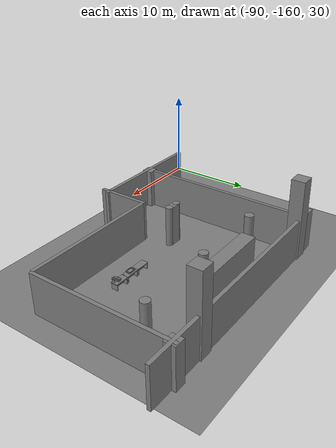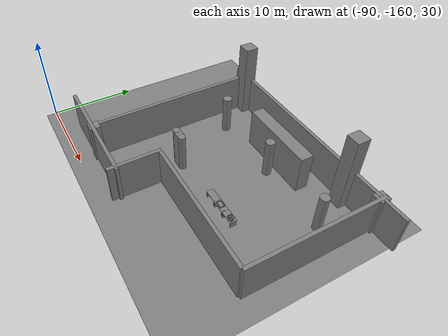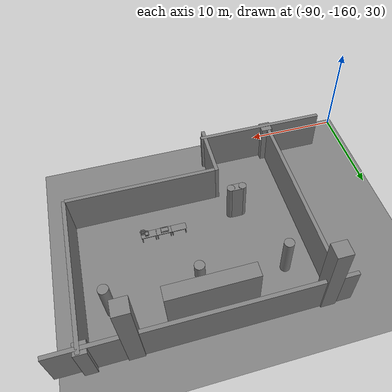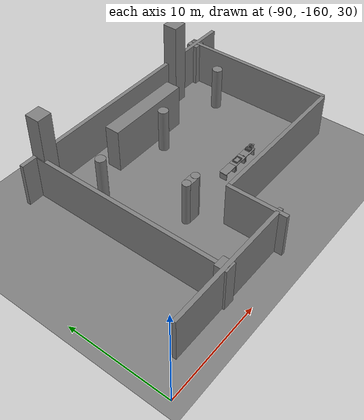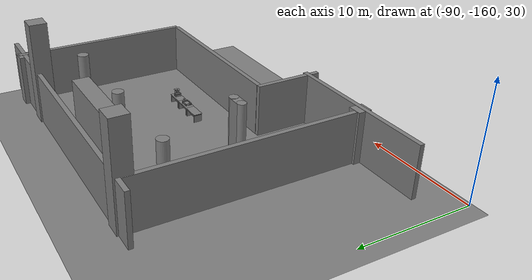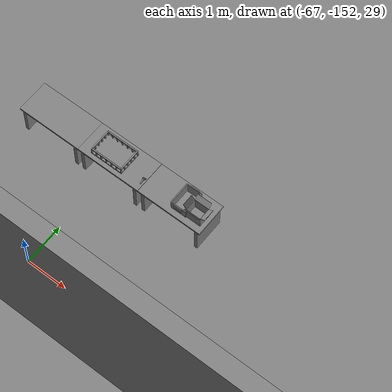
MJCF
<mujoco>
    <option gravity="0.000000000 0.000000000 -9.810000420" timestep="0.0049999999" integrator="implicitfast" density="1.225" viscosity="1.8000001e-05" noslip_iterations="10" iterations="100" sdf_iterations="50">
        <flag multiccd="disable"/>
    </option>
    <size memory="1000M"/>
    <compiler coordinate="local"/>
    <worldbody>
        <light cutoff="30" pos="0 1 1" dir="0 -1 -2"/>
        <light cutoff="30" pos="0 -1 1" dir="0 1 -2"/>
        <body pos="-64.866622925 -149.383972168 30.183746338" euler="89.999992371 89.999946594 0.000000000" name="openloong_gripper_2f85_fix_base_usda_bluebox_01">
            <geom contype="1" conaffinity="1" density="1000" type="box" material="" rgba="0.500000000 0.500000000 0.500000000 1.000000000" solimp="0.899999976 0.949999988 0.001000000" friction="1.000000000 0.005000000 0.000100000" solref="0.020000000 1.000000000" margin="0" condim="3" group="0" pos="0.276596069 0.187225342 0.000061035" quat="0.707107008 0.000077501 0.707106471 0.000077456" size="0.100000001 0.057999998 0.010000000" name="openloong_gripper_2f85_fix_base_usda_geom_C2E59F80_E33E_48BE_9647_9C4F7FDB93F4"/>
            <geom contype="1" conaffinity="1" density="1000" type="box" material="" rgba="0.500000000 0.500000000 0.500000000 1.000000000" solimp="0.899999976 0.949999988 0.001000000" friction="1.000000000 0.005000000 0.000100000" solref="0.020000000 1.000000000" margin="0" condim="3" group="0" pos="0.000000000 0.002883911 0.000000000" quat="1.000000000 0.000000000 0.000000000 0.000000000" size="0.254000008 0.003000000 0.172000006" name="openloong_gripper_2f85_fix_base_usda_geom_9E0ACF15_741B_48D8_BB4E_51487A91DF8E"/>
            <geom contype="1" conaffinity="1" density="1000" type="box" material="" rgba="0.500000000 0.500000000 0.500000000 1.000000000" solimp="0.899999976 0.949999988 0.001000000" friction="1.000000000 0.005000000 0.000100000" solref="0.020000000 1.000000000" margin="0" condim="3" group="0" pos="0.000015259 0.124874115 0.173477173" quat="0.999796450 0.020176515 -0.000000015 0.000000030" size="0.259999990 0.119999997 0.007000000" name="openloong_gripper_2f85_fix_base_usda_geom_383FD9C0_5492_43B2_8078_80B55493434B"/>
            <geom contype="1" conaffinity="1" density="1000" type="box" material="" rgba="0.500000000 0.500000000 0.500000000 1.000000000" solimp="0.899999976 0.949999988 0.001000000" friction="1.000000000 0.005000000 0.000100000" solref="0.020000000 1.000000000" margin="0" condim="3" group="0" pos="0.000015259 0.124874115 -0.173477173" quat="0.999796450 -0.020176545 -0.000000015 0.000000000" size="0.259999990 0.119999997 0.007000000" name="openloong_gripper_2f85_fix_base_usda_geom_C87A77A8_2FA2_4811_A605_D096CF162902"/>
            <geom contype="1" conaffinity="1" density="1000" type="box" material="" rgba="0.500000000 0.500000000 0.500000000 1.000000000" solimp="0.899999976 0.949999988 0.001000000" friction="1.000000000 0.005000000 0.000100000" solref="0.020000000 1.000000000" margin="0" condim="3" group="0" pos="0.000015259 0.214012146 0.188980103" quat="0.999913096 0.013176724 0.000000015 0.000000000" size="0.259999990 0.029999999 0.012500000" name="openloong_gripper_2f85_fix_base_usda_geom_2540EC2F_1D12_4EA9_ACD1_65E2BAF346FA"/>
            <geom contype="1" conaffinity="1" density="1000" type="box" material="" rgba="0.500000000 0.500000000 0.500000000 1.000000000" solimp="0.899999976 0.949999988 0.001000000" friction="1.000000000 0.005000000 0.000100000" solref="0.020000000 1.000000000" margin="0" condim="3" group="0" pos="-0.258346558 0.125289917 0.001876831" quat="0.702796996 -0.020792052 0.710783184 0.020769238" size="0.189999998 0.119999997 0.009000000" name="openloong_gripper_2f85_fix_base_usda_geom_7462894C_E543_414B_8798_83FD395EB048"/>
            <geom contype="1" conaffinity="1" density="1000" type="box" material="" rgba="0.500000000 0.500000000 0.500000000 1.000000000" solimp="0.899999976 0.949999988 0.001000000" friction="1.000000000 0.005000000 0.000100000" solref="0.020000000 1.000000000" margin="0" condim="3" group="0" pos="0.000015259 0.214012146 -0.188980103" quat="0.999913096 -0.013176769 0.000000030 0.000000015" size="0.259999990 0.029999999 0.012500000" name="openloong_gripper_2f85_fix_base_usda_geom_14A5E55C_0B11_4CD8_A9AC_C4D03A5FFC4A"/>
            <geom contype="1" conaffinity="1" density="1000" type="box" material="" rgba="0.500000000 0.500000000 0.500000000 1.000000000" solimp="0.899999976 0.949999988 0.001000000" friction="1.000000000 0.005000000 0.000100000" solref="0.020000000 1.000000000" margin="0" condim="3" group="0" pos="-0.276596069 0.187225342 0.000061035" quat="0.707106650 0.000077441 0.707106709 0.000077456" size="0.100000001 0.057999998 0.010000000" name="openloong_gripper_2f85_fix_base_usda_geom_506D1562_2A3B_4852_B36E_8E7AABBF4CD2"/>
            <geom contype="1" conaffinity="1" density="1000" type="box" material="" rgba="0.500000000 0.500000000 0.500000000 1.000000000" solimp="0.899999976 0.949999988 0.001000000" friction="1.000000000 0.005000000 0.000100000" solref="0.020000000 1.000000000" margin="0" condim="3" group="0" pos="0.258346558 0.125289917 0.001876831" quat="0.702851534 0.018856451 0.710823834 -0.019329429" size="0.189999998 0.119999997 0.009000000" name="openloong_gripper_2f85_fix_base_usda_geom_437885E4_5C43_41A2_8C4C_E5658BDBE4A5"/>
            <freejoint name="openloong_gripper_2f85_fix_base_usda_bluebox_01_joint"/>
            <site size="0.005000000 0.005000000 0.005000000" rgba="0.500000000 0.500000000 0.500000000 1.000000000" pos="0.000000000 0.000000000 0.000000000" quat="0.999961913 0.008726534 0.000000000 0.000000000" group="0" type="sphere" name="openloong_gripper_2f85_fix_base_usda_bluebox_01site"/>
        </body>
        <body pos="-64.496299744 -149.491867065 30.235729218" euler="0.000000000 0.000000000 89.999946594" name="openloong_gripper_2f85_fix_base_usda_cardboardbox_01">
            <geom contype="1" conaffinity="1" density="1000" type="box" material="" rgba="0.500000000 0.500000000 0.500000000 1.000000000" solimp="0.899999976 0.949999988 0.001000000" friction="1.000000000 0.005000000 0.000100000" solref="0.020000000 1.000000000" margin="0" condim="3" group="0" pos="-0.003166199 -0.004086494 0.005052090" quat="1.000000000 0.000000000 0.000000000 0.000000000" size="0.142499998 0.177500010 0.005000000" name="openloong_gripper_2f85_fix_base_usda_geom_2DDA939E_7D16_4F51_8859_9BD63298CFFE"/>
            <geom contype="1" conaffinity="1" density="1000" type="box" material="" rgba="0.500000000 0.500000000 0.500000000 1.000000000" solimp="0.899999976 0.949999988 0.001000000" friction="1.000000000 0.005000000 0.000100000" solref="0.020000000 1.000000000" margin="0" condim="3" group="0" pos="-0.003166199 0.170316696 0.150570869" quat="1.000000000 0.000000000 0.000000000 0.000000000" size="0.142499998 0.005000000 0.149999991" name="openloong_gripper_2f85_fix_base_usda_geom_EF2B8ECF_007A_42FB_A4ED_D4250012212C"/>
            <geom contype="1" conaffinity="1" density="1000" type="box" material="" rgba="0.500000000 0.500000000 0.500000000 1.000000000" solimp="0.899999976 0.949999988 0.001000000" friction="1.000000000 0.005000000 0.000100000" solref="0.020000000 1.000000000" margin="0" condim="3" group="0" pos="-0.147399902 -0.005307198 0.150570869" quat="1.000000000 0.000000000 0.000000000 0.000000000" size="0.005000000 0.177500010 0.149999991" name="openloong_gripper_2f85_fix_base_usda_geom_9B7DEA59_1F2F_4E5B_A17A_B5E353D244B9"/>
            <geom contype="1" conaffinity="1" density="1000" type="box" material="" rgba="0.500000000 0.500000000 0.500000000 1.000000000" solimp="0.899999976 0.949999988 0.001000000" friction="1.000000000 0.005000000 0.000100000" solref="0.020000000 1.000000000" margin="0" condim="3" group="0" pos="0.140275955 -0.005307198 0.150570869" quat="1.000000000 0.000000000 0.000000000 0.000000000" size="0.005000000 0.177500010 0.149999991" name="openloong_gripper_2f85_fix_base_usda_geom_2DAD9A29_F507_4934_B5F7_2076EDB7D58C"/>
            <geom contype="1" conaffinity="1" density="1000" type="box" material="" rgba="0.500000000 0.500000000 0.500000000 1.000000000" solimp="0.899999976 0.949999988 0.001000000" friction="1.000000000 0.005000000 0.000100000" solref="0.020000000 1.000000000" margin="0" condim="3" group="0" pos="-0.003166199 -0.181550980 0.150570869" quat="1.000000000 0.000000000 0.000000000 0.000000000" size="0.142499998 0.005000000 0.149999991" name="openloong_gripper_2f85_fix_base_usda_geom_EB8FF862_19F2_4A73_B59B_439169C30A32"/>
            <freejoint name="openloong_gripper_2f85_fix_base_usda_cardboardbox_01_joint"/>
            <site size="0.005000000 0.005000000 0.005000000" rgba="0.500000000 0.500000000 0.500000000 1.000000000" pos="0.000000000 0.000000000 0.000000000" quat="0.999961913 0.008726535 0.000000000 0.000000000" group="0" type="sphere" name="openloong_gripper_2f85_fix_base_usda_site_801641BE_D6A1_4DB0_A7AB_0075E58335BE"/>
            <body pos="0.139160156 -0.004048347 0.301930904" euler="-179.999954224 49.383502960 179.999954224" name="openloong_gripper_2f85_fix_base_usda_A1_006">
                <geom contype="1" conaffinity="1" density="1000" type="box" material="" rgba="0.500000000 0.500000000 0.500000000 1.000000000" solimp="0.899999976 0.949999988 0.001000000" friction="1.000000000 0.005000000 0.000100000" solref="0.020000000 1.000000000" margin="0" condim="3" group="0" pos="-0.071587563 0.000009537 0.001745224" quat="0.999999881 0.000000000 0.000000000 0.000000000" size="0.071249999 0.179999992 0.002500000" name="openloong_gripper_2f85_fix_base_usda_geom_6542EBE0_BD07_4A26_B43A_1D7A7FB6474B"/>
                <joint armature="0" stiffness="0.07" damping="0.0099999998" axis="0.000000 1.000000 0.000000" type="hinge" name="openloong_gripper_2f85_fix_base_usda_A1_006"/>
            </body>
            <body pos="-0.145902634 -0.004086494 0.301938057" euler="-180.000000000 -60.000011444 -180.000000000" name="openloong_gripper_2f85_fix_base_usda_A2_006">
                <geom contype="1" conaffinity="1" density="1000" type="box" material="" rgba="0.500000000 0.500000000 0.500000000 1.000000000" solimp="0.899999976 0.949999988 0.001000000" friction="1.000000000 0.005000000 0.000100000" solref="0.020000000 1.000000000" margin="0" condim="3" group="0" pos="0.071268082 0.000009537 0.002717972" quat="0.000002921 0.000000000 -0.000000030 0.999999881" size="0.071249999 0.179999992 0.002500000" name="openloong_gripper_2f85_fix_base_usda_geom_ECEE350E_D9C0_4E4D_8599_631B882985C0"/>
                <joint armature="0" stiffness="0.07" damping="0.0099999998" axis="0.000000 1.000000 0.000000" type="hinge" name="openloong_gripper_2f85_fix_base_usda_A2_006"/>
            </body>
            <body pos="-0.003385544 0.175991058 0.301930904" euler="-125.858116150 -0.000004561 0.000002331" name="openloong_gripper_2f85_fix_base_usda_B2_006">
                <geom contype="1" conaffinity="1" density="1000" type="box" material="" rgba="0.500000000 0.500000000 0.500000000 1.000000000" solimp="0.899999976 0.949999988 0.001000000" friction="1.000000000 0.005000000 0.000100000" solref="0.020000000 1.000000000" margin="0" condim="3" group="0" pos="0.000009537 -0.070939064 -0.002470016" quat="0.999614120 0.027776197 -0.000000015 0.000000030" size="0.137500003 0.064999998 0.005000000" name="openloong_gripper_2f85_fix_base_usda_geom_482F3A48_9C9C_48D6_ACE5_EFF6A7B8170D"/>
                <joint armature="0" stiffness="0.07" damping="0.0099999998" axis="1.000000 0.000000 0.000000" type="hinge" name="openloong_gripper_2f85_fix_base_usda_B2_006"/>
            </body>
            <body pos="-0.003385544 -0.184140205 0.301938057" euler="147.805557251 0.000000000 0.000000000" name="openloong_gripper_2f85_fix_base_usda_B1_006">
                <geom contype="1" conaffinity="1" density="1000" type="box" material="" rgba="0.500000000 0.500000000 0.500000000 1.000000000" solimp="0.899999976 0.949999988 0.001000000" friction="1.000000000 0.005000000 0.000100000" solref="0.020000000 1.000000000" margin="0" condim="3" group="0" pos="-0.000028610 0.070202351 -0.002703667" quat="0.999614179 -0.027776167 0.000000000 0.000000000" size="0.137500003 0.064999998 0.005000000" name="openloong_gripper_2f85_fix_base_usda_geom_03373F96_4C04_4556_994F_F310DFAE52F8"/>
                <joint armature="0" stiffness="0.07" damping="0.0099999998" axis="1.000000 0.000000 0.000000" type="hinge" name="openloong_gripper_2f85_fix_base_usda_B1_006"/>
            </body>
        </body>
        <body pos="-65.882858276 -149.481979370 30.229999542" euler="-64.487716675 0.000000000 0.000000000" name="openloong_gripper_2f85_fix_base_usda_Barcode">
            <geom contype="1" conaffinity="1" density="1000" type="box" material="" rgba="0.500000000 0.500000000 0.500000000 1.000000000" solimp="0.899999976 0.949999988 0.001000000" friction="1.000000000 0.005000000 0.000100000" solref="0.020000000 1.000000000" margin="0" condim="3" group="0" pos="0.000000000 0.013038635 0.001419067" quat="0.000000000 0.000000000 0.000000000 1.000000119" size="0.034000002 0.010000000 0.017999999" name="openloong_gripper_2f85_fix_base_usda_geom_B28763E5_4CBC_4088_9B9A_3AAAB311F7B8"/>
            <geom contype="1" conaffinity="1" density="1000" type="box" material="" rgba="0.500000000 0.500000000 0.500000000 1.000000000" solimp="0.899999976 0.949999988 0.001000000" friction="1.000000000 0.005000000 0.000100000" solref="0.020000000 1.000000000" margin="0" condim="3" group="0" pos="0.000000000 -0.035301208 -0.007095337" quat="0.000000000 0.000000000 -0.043619365 0.999048233" size="0.028999999 0.010000000 0.020000000" name="openloong_gripper_2f85_fix_base_usda_geom_DC588FED_7A89_4D03_ADF8_77999EC19063"/>
            <geom contype="1" conaffinity="1" density="1000" type="box" material="" rgba="0.500000000 0.500000000 0.500000000 1.000000000" solimp="0.899999976 0.949999988 0.001000000" friction="1.000000000 0.005000000 0.000100000" solref="0.020000000 1.000000000" margin="0" condim="3" group="0" pos="0.000000000 -0.043411255 -0.011749268" quat="0.922262907 0.386563420 0.000000000 0.000000000" size="0.026000001 0.010000000 0.020000000" name="openloong_gripper_2f85_fix_base_usda_geom_81E9ACFD_7396_46B2_BE75_278E7FA16A6A"/>
            <geom contype="1" conaffinity="1" density="1000" type="box" material="" rgba="0.500000000 0.500000000 0.500000000 1.000000000" solimp="0.899999976 0.949999988 0.001000000" friction="1.000000000 0.005000000 0.000100000" solref="0.020000000 1.000000000" margin="0" condim="3" group="0" pos="0.000000000 -0.016967773 -0.031860352" quat="0.000000000 0.000000000 0.000000000 1.000000119" size="0.008000000 0.010000000 0.013000000" name="openloong_gripper_2f85_fix_base_usda_geom_E820BC1A_14B2_4B26_9E8F_A5CDF86F681E"/>
            <geom contype="1" conaffinity="1" density="1000" type="box" material="" rgba="0.500000000 0.500000000 0.500000000 1.000000000" solimp="0.899999976 0.949999988 0.001000000" friction="1.000000000 0.005000000 0.000100000" solref="0.020000000 1.000000000" margin="0" condim="3" group="0" pos="0.000000000 -0.001869202 0.000312805" quat="0.953716993 0.300705761 0.000000000 0.000000000" size="0.032000002 0.010000000 0.018999999" name="openloong_gripper_2f85_fix_base_usda_geom_AEAE5AB2_87A8_4C3A_B2F6_DDD7F11B8884"/>
            <geom contype="1" conaffinity="1" density="1000" type="box" material="" rgba="0.500000000 0.500000000 0.500000000 1.000000000" solimp="0.899999976 0.949999988 0.001000000" friction="1.000000000 0.005000000 0.000100000" solref="0.020000000 1.000000000" margin="0" condim="3" group="0" pos="0.000000000 -0.019531250 -0.003173828" quat="0.953716993 0.300705761 0.000000000 0.000000000" size="0.030999999 0.010000000 0.020000000" name="openloong_gripper_2f85_fix_base_usda_geom_0AEC1233_AD2B_4F55_B85A_959C1047A69D"/>
            <geom contype="1" conaffinity="1" density="1000" type="box" material="" rgba="0.500000000 0.500000000 0.500000000 1.000000000" solimp="0.899999976 0.949999988 0.001000000" friction="1.000000000 0.005000000 0.000100000" solref="0.020000000 1.000000000" margin="0" condim="3" group="0" pos="0.000000000 -0.035301208 -0.007095337" quat="0.953716993 0.300705761 0.000000000 0.000000000" size="0.028999999 0.010000000 0.020000000" name="openloong_gripper_2f85_fix_base_usda_geom_7D0F8615_CB5C_4EB3_A54C_EEC345166A51"/>
            <geom contype="1" conaffinity="1" density="1000" type="box" material="" rgba="0.500000000 0.500000000 0.500000000 1.000000000" solimp="0.899999976 0.949999988 0.001000000" friction="1.000000000 0.005000000 0.000100000" solref="0.020000000 1.000000000" margin="0" condim="3" group="0" pos="0.000000000 -0.042617798 -0.071121216" quat="0.000000000 0.000000000 0.000000000 1.000000119" size="0.013000000 0.021000000 0.059999999" name="openloong_gripper_2f85_fix_base_usda_geom_9A037B57_3191_4596_941A_ED269396CA99"/>
            <freejoint name="openloong_gripper_2f85_fix_base_usda_Barcode_joint"/>
            <site size="0.005000000 0.005000000 0.005000000" rgba="0.500000000 0.500000000 0.500000000 1.000000000" pos="0.000000000 0.000000000 0.000000000" quat="1.000000000 0.000000000 0.000000000 0.000000000" group="0" type="sphere" name="openloong_gripper_2f85_fix_base_usda_Barcode_site"/>
        </body>
        <body pos="-66.745018005 -149.392349243 30.184000015" euler="0.000000000 0.000000000 89.999946594" name="[22333206980324]_Basket_01">
            <geom contype="1" conaffinity="1" density="1000" type="box" material="" rgba="0.500000000 0.500000000 0.500000000 1.000000000" solimp="0.899999976 0.949999988 0.001000000" friction="1.000000000 0.005000000 0.000100000" solref="0.020000000 1.000000000" margin="0" condim="3" group="0" pos="-0.052425385 0.389207840 0.089787483" quat="0.707107008 0.000000000 0.000000000 0.707106411" size="0.014249999 0.014249999 0.059999999" name="[22333206980324]_geom_59AC212F_2016_48C8_BCDF_BDDFA8CF38BF"/>
            <geom contype="1" conaffinity="1" density="1000" type="box" material="" rgba="0.500000000 0.500000000 0.500000000 1.000000000" solimp="0.899999976 0.949999988 0.001000000" friction="1.000000000 0.005000000 0.000100000" solref="0.020000000 1.000000000" margin="0" condim="3" group="0" pos="0.264015198 -0.133043289 0.089787483" quat="0.707107008 0.000000000 0.000000000 0.707106411" size="0.014249999 0.014249999 0.059999999" name="[22333206980324]_geom_109BD4F2_525E_4AEF_9627_9186AF99432A"/>
            <geom contype="1" conaffinity="1" density="1000" type="box" material="" rgba="0.500000000 0.500000000 0.500000000 1.000000000" solimp="0.899999976 0.949999988 0.001000000" friction="1.000000000 0.005000000 0.000100000" solref="0.020000000 1.000000000" margin="0" condim="3" group="0" pos="-0.264015198 -0.265548706 0.089793205" quat="0.707107008 0.000000000 0.000000000 0.707106411" size="0.014249999 0.014249999 0.059999999" name="[22333206980324]_geom_593FF122_B274_48E7_9B0A_3E859E7D8DA3"/>
            <geom contype="1" conaffinity="1" density="1000" type="box" material="" rgba="0.500000000 0.500000000 0.500000000 1.000000000" solimp="0.899999976 0.949999988 0.001000000" friction="1.000000000 0.005000000 0.000100000" solref="0.020000000 1.000000000" margin="0" condim="3" group="0" pos="-0.160263062 -0.389322281 0.089793205" quat="0.707107008 0.000000000 0.000000000 0.707106411" size="0.014249999 0.014249999 0.059999999" name="[22333206980324]_geom_DD0E7ABA_5F17_4037_8618_DCF585EAAD57"/>
            <geom contype="1" conaffinity="1" density="1000" type="box" material="" rgba="0.500000000 0.500000000 0.500000000 1.000000000" solimp="0.899999976 0.949999988 0.001000000" friction="1.000000000 0.005000000 0.000100000" solref="0.020000000 1.000000000" margin="0" condim="3" group="0" pos="0.162265778 -0.389322281 0.089787483" quat="0.707107008 0.000000000 0.000000000 0.707106411" size="0.014249999 0.014249999 0.059999999" name="[22333206980324]_geom_F62E62E4_7DBC_44DD_99E2_0B2759E6FEAC"/>
            <geom contype="1" conaffinity="1" density="1000" type="box" material="" rgba="0.500000000 0.500000000 0.500000000 1.000000000" solimp="0.899999976 0.949999988 0.001000000" friction="1.000000000 0.005000000 0.000100000" solref="0.020000000 1.000000000" margin="0" condim="3" group="0" pos="0.264015198 0.389207840 0.089787483" quat="0.707107008 0.000000000 0.000000000 0.707106411" size="0.014249999 0.014249999 0.059999999" name="[22333206980324]_geom_724F46FA_2F32_43BD_8B17_F513083AB4D9"/>
            <geom contype="1" conaffinity="1" density="1000" type="box" material="" rgba="0.500000000 0.500000000 0.500000000 1.000000000" solimp="0.899999976 0.949999988 0.001000000" friction="1.000000000 0.005000000 0.000100000" solref="0.020000000 1.000000000" margin="0" condim="3" group="0" pos="-0.264015198 -0.133043289 0.089793205" quat="0.707107008 0.000000000 0.000000000 0.707106411" size="0.014249999 0.014249999 0.059999999" name="[22333206980324]_geom_F4F71A00_4779_464D_83DD_D8B9640A3036"/>
            <geom contype="1" conaffinity="1" density="1000" type="box" material="" rgba="0.500000000 0.500000000 0.500000000 1.000000000" solimp="0.899999976 0.949999988 0.001000000" friction="1.000000000 0.005000000 0.000100000" solref="0.020000000 1.000000000" margin="0" condim="3" group="0" pos="-0.264026642 0.269256592 0.089793205" quat="0.707107008 0.000000000 0.000000000 0.707106411" size="0.014249999 0.014249999 0.059999999" name="[22333206980324]_geom_6F1D3EE6_875C_4B7A_80F1_C1B3DFDA386C"/>
            <geom contype="1" conaffinity="1" density="1000" type="box" material="" rgba="0.500000000 0.500000000 0.500000000 1.000000000" solimp="0.899999976 0.949999988 0.001000000" friction="1.000000000 0.005000000 0.000100000" solref="0.020000000 1.000000000" margin="0" condim="3" group="0" pos="0.054462433 0.389207840 0.089787483" quat="0.707107008 0.000000000 0.000000000 0.707106411" size="0.014249999 0.014249999 0.059999999" name="[22333206980324]_geom_469E656B_3E31_4DBB_BA52_36F3F2A4D724"/>
            <geom contype="1" conaffinity="1" density="1000" type="box" material="" rgba="0.500000000 0.500000000 0.500000000 1.000000000" solimp="0.899999976 0.949999988 0.001000000" friction="1.000000000 0.005000000 0.000100000" solref="0.020000000 1.000000000" margin="0" condim="3" group="0" pos="0.054462433 -0.389322281 0.089787483" quat="0.707107008 0.000000000 0.000000000 0.707106411" size="0.014249999 0.014249999 0.059999999" name="[22333206980324]_geom_B969A978_8D8F_4830_AC6B_30D69798017F"/>
            <geom contype="1" conaffinity="1" density="1000" type="box" material="" rgba="0.500000000 0.500000000 0.500000000 1.000000000" solimp="0.899999976 0.949999988 0.001000000" friction="1.000000000 0.005000000 0.000100000" solref="0.020000000 1.000000000" margin="0" condim="3" group="0" pos="0.264015198 0.269256592 0.089793205" quat="0.707107008 0.000000000 0.000000000 0.707106411" size="0.014249999 0.014249999 0.059999999" name="[22333206980324]_geom_091EB1BC_98B7_40A4_959C_175F69A11700"/>
            <geom contype="1" conaffinity="1" density="1000" type="box" material="" rgba="0.500000000 0.500000000 0.500000000 1.000000000" solimp="0.899999976 0.949999988 0.001000000" friction="1.000000000 0.005000000 0.000100000" solref="0.020000000 1.000000000" margin="0" condim="3" group="0" pos="0.264015198 -0.389322281 0.089787483" quat="0.707107008 0.000000000 0.000000000 0.707106411" size="0.014249999 0.014249999 0.059999999" name="[22333206980324]_geom_336013D9_C004_40FE_9684_273EB5093DC6"/>
            <geom contype="1" conaffinity="1" density="1000" type="box" material="" rgba="0.500000000 0.500000000 0.500000000 1.000000000" solimp="0.899999976 0.949999988 0.001000000" friction="1.000000000 0.005000000 0.000100000" solref="0.020000000 1.000000000" margin="0" condim="3" group="0" pos="0.000000000 0.000000000 0.015998840" quat="0.707107008 0.000000000 0.000000000 0.707106411" size="0.403499991 0.279000014 0.015750000" name="[22333206980324]_geom_1E69B917_3C0A_46E3_BC70_46A1C1FA9EA5"/>
            <geom contype="1" conaffinity="1" density="1000" type="box" material="" rgba="0.500000000 0.500000000 0.500000000 1.000000000" solimp="0.899999976 0.949999988 0.001000000" friction="1.000000000 0.005000000 0.000100000" solref="0.020000000 1.000000000" margin="0" condim="3" group="0" pos="0.000000000 -0.389476776 0.163619041" quat="0.707107008 0.000000000 0.000000000 0.707106411" size="0.015000000 0.277500004 0.015750000" name="[22333206980324]_geom_0481CEA0_DD69_4DD8_9247_8AB6D5DF4BFA"/>
            <geom contype="1" conaffinity="1" density="1000" type="box" material="" rgba="0.500000000 0.500000000 0.500000000 1.000000000" solimp="0.899999976 0.949999988 0.001000000" friction="1.000000000 0.005000000 0.000100000" solref="0.020000000 1.000000000" margin="0" condim="3" group="0" pos="0.162265778 0.389207840 0.089787483" quat="0.707107008 0.000000000 0.000000000 0.707106411" size="0.014249999 0.014249999 0.059999999" name="[22333206980324]_geom_00B9A4AB_1789_43D5_A9FF_1BFB6BAE034D"/>
            <geom contype="1" conaffinity="1" density="1000" type="box" material="" rgba="0.500000000 0.500000000 0.500000000 1.000000000" solimp="0.899999976 0.949999988 0.001000000" friction="1.000000000 0.005000000 0.000100000" solref="0.020000000 1.000000000" margin="0" condim="3" group="0" pos="0.000000000 0.389471054 0.163619041" quat="0.707107008 0.000000000 0.000000000 0.707106411" size="0.015000000 0.277500004 0.015750000" name="[22333206980324]_geom_FF91AEA1_61B6_4910_B710_B25A19E784B4"/>
            <geom contype="1" conaffinity="1" density="1000" type="box" material="" rgba="0.500000000 0.500000000 0.500000000 1.000000000" solimp="0.899999976 0.949999988 0.001000000" friction="1.000000000 0.005000000 0.000100000" solref="0.020000000 1.000000000" margin="0" condim="3" group="0" pos="-0.263511658 0.000000000 0.163619041" quat="0.707107008 0.000000000 0.000000000 0.707106411" size="0.403499991 0.015000000 0.015750000" name="[22333206980324]_geom_1D9E12F3_A344_415A_8B4B_07EB5BD9AF41"/>
            <geom contype="1" conaffinity="1" density="1000" type="box" material="" rgba="0.500000000 0.500000000 0.500000000 1.000000000" solimp="0.899999976 0.949999988 0.001000000" friction="1.000000000 0.005000000 0.000100000" solref="0.020000000 1.000000000" margin="0" condim="3" group="0" pos="-0.264015198 0.141334534 0.089793205" quat="0.707107008 0.000000000 0.000000000 0.707106411" size="0.014249999 0.014249999 0.059999999" name="[22333206980324]_geom_E42AED69_BD07_4354_829D_0CF56FB1518F"/>
            <geom contype="1" conaffinity="1" density="1000" type="box" material="" rgba="0.500000000 0.500000000 0.500000000 1.000000000" solimp="0.899999976 0.949999988 0.001000000" friction="1.000000000 0.005000000 0.000100000" solref="0.020000000 1.000000000" margin="0" condim="3" group="0" pos="0.264015198 -0.265548706 0.089787483" quat="0.707107008 0.000000000 0.000000000 0.707106411" size="0.014249999 0.014249999 0.059999999" name="[22333206980324]_geom_D7FBB939_E7C1_440C_8F11_487F2033C3FE"/>
            <geom contype="1" conaffinity="1" density="1000" type="box" material="" rgba="0.500000000 0.500000000 0.500000000 1.000000000" solimp="0.899999976 0.949999988 0.001000000" friction="1.000000000 0.005000000 0.000100000" solref="0.020000000 1.000000000" margin="0" condim="3" group="0" pos="-0.160263062 0.389207840 0.089787483" quat="0.707107008 0.000000000 0.000000000 0.707106411" size="0.014249999 0.014249999 0.059999999" name="[22333206980324]_geom_DB3E1D65_0C41_4375_94D4_C0858EDB7FA9"/>
            <geom contype="1" conaffinity="1" density="1000" type="box" material="" rgba="0.500000000 0.500000000 0.500000000 1.000000000" solimp="0.899999976 0.949999988 0.001000000" friction="1.000000000 0.005000000 0.000100000" solref="0.020000000 1.000000000" margin="0" condim="3" group="0" pos="-0.052425385 -0.389322281 0.089787483" quat="0.707107008 0.000000000 0.000000000 0.707106411" size="0.014249999 0.014249999 0.059999999" name="[22333206980324]_geom_56701943_CCEE_4288_9BF4_5FE036440646"/>
            <geom contype="1" conaffinity="1" density="1000" type="box" material="" rgba="0.500000000 0.500000000 0.500000000 1.000000000" solimp="0.899999976 0.949999988 0.001000000" friction="1.000000000 0.005000000 0.000100000" solref="0.020000000 1.000000000" margin="0" condim="3" group="0" pos="-0.264026642 -0.389322281 0.089793205" quat="0.707107008 0.000000000 0.000000000 0.707106411" size="0.014249999 0.014249999 0.059999999" name="[22333206980324]_geom_8283E137_15E3_448A_909A_2FFA4F419816"/>
            <geom contype="1" conaffinity="1" density="1000" type="box" material="" rgba="0.500000000 0.500000000 0.500000000 1.000000000" solimp="0.899999976 0.949999988 0.001000000" friction="1.000000000 0.005000000 0.000100000" solref="0.020000000 1.000000000" margin="0" condim="3" group="0" pos="0.264015198 0.141334534 0.089787483" quat="0.707107008 0.000000000 0.000000000 0.707106411" size="0.014249999 0.014249999 0.059999999" name="[22333206980324]_geom_23B172FC_DE90_435F_BA27_BDC0360CD97E"/>
            <geom contype="1" conaffinity="1" density="1000" type="box" material="" rgba="0.500000000 0.500000000 0.500000000 1.000000000" solimp="0.899999976 0.949999988 0.001000000" friction="1.000000000 0.005000000 0.000100000" solref="0.020000000 1.000000000" margin="0" condim="3" group="0" pos="-0.264015198 0.389207840 0.089793205" quat="0.707107008 0.000000000 0.000000000 0.707106411" size="0.014249999 0.014249999 0.059999999" name="[22333206980324]_geom_F92B7854_6425_4B4F_B543_F1A815E6AA5C"/>
            <geom contype="1" conaffinity="1" density="1000" type="box" material="" rgba="0.500000000 0.500000000 0.500000000 1.000000000" solimp="0.899999976 0.949999988 0.001000000" friction="1.000000000 0.005000000 0.000100000" solref="0.020000000 1.000000000" margin="0" condim="3" group="0" pos="0.264015198 0.004480362 0.089787483" quat="0.707107008 0.000000000 0.000000000 0.707106411" size="0.014249999 0.014249999 0.059999999" name="[22333206980324]_geom_09E5B643_6041_491B_9547_2488C5DD7AAE"/>
            <geom contype="1" conaffinity="1" density="1000" type="box" material="" rgba="0.500000000 0.500000000 0.500000000 1.000000000" solimp="0.899999976 0.949999988 0.001000000" friction="1.000000000 0.005000000 0.000100000" solref="0.020000000 1.000000000" margin="0" condim="3" group="0" pos="0.263694763 -0.000011444 0.163619041" quat="0.707107008 0.000000000 0.000000000 0.707106411" size="0.403499991 0.015000000 0.015750000" name="[22333206980324]_geom_3A5560EB_4EB5_4501_82F2_574C8569F36A"/>
            <geom contype="1" conaffinity="1" density="1000" type="box" material="" rgba="0.500000000 0.500000000 0.500000000 1.000000000" solimp="0.899999976 0.949999988 0.001000000" friction="1.000000000 0.005000000 0.000100000" solref="0.020000000 1.000000000" margin="0" condim="3" group="0" pos="-0.264015198 0.004480362 0.089793205" quat="0.707107008 0.000000000 0.000000000 0.707106411" size="0.014249999 0.014249999 0.059999999" name="[22333206980324]_geom_DD9D1AC4_70A3_4DF3_9911_2D76E35F7E4C"/>
            <freejoint name="[22333206980324]_joint_60016638_16ED_4F19_B000_E1C161BC16D0"/>
        </body>
        <body pos="0.000000000 0.000000000 0.000000000" euler="0.000000000 0.000000000 0.000000000" name="Static Objects_Static Objects">
            <geom contype="1" conaffinity="1" density="1000" type="box" material="" rgba="0.500000000 0.500000000 0.500000000 1.000000000" solimp="0.899999976 0.949999988 0.001000000" friction="1.000000000 0.005000000 0.000100000" solref="0.020000000 1.000000000" margin="0" condim="3" group="0" pos="-67.544113159 -149.365814209 29.727830887" quat="0.500000417 0.499999970 0.499999553 0.499999970" size="0.381000012 0.319999993 0.041000001" name="Static Objects_geom_59864C49_DAE9_48F6_8BE8_5E7CAE46C8F8"/>
            <geom contype="1" conaffinity="1" density="1000" type="box" material="" rgba="0.500000000 0.500000000 0.500000000 1.000000000" solimp="0.899999976 0.949999988 0.001000000" friction="1.000000000 0.005000000 0.000100000" solref="0.020000000 1.000000000" margin="0" condim="3" group="0" pos="-68.239501953 -149.365814209 30.086868286" quat="0.500000417 0.499999970 0.499999553 0.499999970" size="0.370999992 0.039500002 0.745000005" name="Static Objects_geom_936729CB_A72C_441D_BA87_AFE5542EF5A0"/>
            <geom contype="1" conaffinity="1" density="1000" type="box" material="" rgba="0.500000000 0.500000000 0.500000000 1.000000000" solimp="0.899999976 0.949999988 0.001000000" friction="1.000000000 0.005000000 0.000100000" solref="0.020000000 1.000000000" margin="0" condim="3" group="0" pos="-68.239501953 -149.365814209 30.147235870" quat="0.500000417 0.499999970 0.499999553 0.499999970" size="0.400000006 0.022000000 0.800000012" name="Static Objects_geom_09D021C0_BDA1_411E_972B_45CC9BD13DDA"/>
            <geom contype="1" conaffinity="1" density="1000" type="box" material="" rgba="0.500000000 0.500000000 0.500000000 1.000000000" solimp="0.899999976 0.949999988 0.001000000" friction="1.000000000 0.005000000 0.000100000" solref="0.020000000 1.000000000" margin="0" condim="3" group="0" pos="-68.934890747 -149.365814209 29.727830887" quat="0.500000417 0.499999970 0.499999553 0.499999970" size="0.381000012 0.319999993 0.041000001" name="Static Objects_geom_88510ECD_6FBF_4807_BCA5_52540AE12EE9"/>
            <geom contype="1" conaffinity="1" density="1000" type="box" material="" rgba="0.500000000 0.500000000 0.500000000 1.000000000" solimp="0.899999976 0.949999988 0.001000000" friction="1.000000000 0.005000000 0.000100000" solref="0.020000000 1.000000000" margin="0" condim="3" group="0" pos="-68.239501953 -149.365814209 29.561563492" quat="0.500000417 0.499999970 0.499999553 0.499999970" size="0.020000000 0.022000000 0.660000026" name="Static Objects_geom_C1F91106_5283_4852_A934_1BC722E85A62"/>
            <geom contype="1" conaffinity="1" density="1000" type="box" material="" rgba="0.500000000 0.500000000 0.500000000 1.000000000" solimp="0.899999976 0.949999988 0.001000000" friction="1.000000000 0.005000000 0.000100000" solref="0.020000000 1.000000000" margin="0" condim="3" group="0" pos="-65.945671082 -149.365814209 29.727830887" quat="0.500000417 0.499999970 0.499999553 0.499999970" size="0.381000012 0.319999993 0.041000001" name="Static Objects_geom_C2D4CAD8_8465_44E5_81CF_27D9852B55EF"/>
            <geom contype="1" conaffinity="1" density="1000" type="box" material="" rgba="0.500000000 0.500000000 0.500000000 1.000000000" solimp="0.899999976 0.949999988 0.001000000" friction="1.000000000 0.005000000 0.000100000" solref="0.020000000 1.000000000" margin="0" condim="3" group="0" pos="-66.641059875 -149.365814209 30.086868286" quat="0.500000417 0.499999970 0.499999553 0.499999970" size="0.370999992 0.039500002 0.745000005" name="Static Objects_geom_E5BB98BC_17D4_47F4_8EBE_480728100C32"/>
            <geom contype="1" conaffinity="1" density="1000" type="box" material="" rgba="0.500000000 0.500000000 0.500000000 1.000000000" solimp="0.899999976 0.949999988 0.001000000" friction="1.000000000 0.005000000 0.000100000" solref="0.020000000 1.000000000" margin="0" condim="3" group="0" pos="-66.641059875 -149.365814209 30.147235870" quat="0.500000417 0.499999970 0.499999553 0.499999970" size="0.400000006 0.022000000 0.800000012" name="Static Objects_geom_56044278_9B52_4350_A376_4E0312BCB20B"/>
            <geom contype="1" conaffinity="1" density="1000" type="box" material="" rgba="0.500000000 0.500000000 0.500000000 1.000000000" solimp="0.899999976 0.949999988 0.001000000" friction="1.000000000 0.005000000 0.000100000" solref="0.020000000 1.000000000" margin="0" condim="3" group="0" pos="-67.336448669 -149.365814209 29.727830887" quat="0.500000417 0.499999970 0.499999553 0.499999970" size="0.381000012 0.319999993 0.041000001" name="Static Objects_geom_7BA35DB9_0CCA_4882_9AD1_659EEFA18562"/>
            <geom contype="1" conaffinity="1" density="1000" type="box" material="" rgba="0.500000000 0.500000000 0.500000000 1.000000000" solimp="0.899999976 0.949999988 0.001000000" friction="1.000000000 0.005000000 0.000100000" solref="0.020000000 1.000000000" margin="0" condim="3" group="0" pos="-66.641059875 -149.365814209 29.561563492" quat="0.500000417 0.499999970 0.499999553 0.499999970" size="0.020000000 0.022000000 0.660000026" name="Static Objects_geom_5AC8A59D_97C2_4BB8_B60E_8FE795F0EF22"/>
            <geom contype="1" conaffinity="1" density="1000" type="box" material="" rgba="0.500000000 0.500000000 0.500000000 1.000000000" solimp="0.899999976 0.949999988 0.001000000" friction="1.000000000 0.005000000 0.000100000" solref="0.020000000 1.000000000" margin="0" condim="3" group="0" pos="-64.338577271 -149.365814209 29.727830887" quat="0.500000417 0.499999970 0.499999553 0.499999970" size="0.381000012 0.319999993 0.041000001" name="Static Objects_geom_520BB0E8_FA2A_4851_9239_E2E0928D349B"/>
            <geom contype="1" conaffinity="1" density="1000" type="box" material="" rgba="0.500000000 0.500000000 0.500000000 1.000000000" solimp="0.899999976 0.949999988 0.001000000" friction="1.000000000 0.005000000 0.000100000" solref="0.020000000 1.000000000" margin="0" condim="3" group="0" pos="-65.033966064 -149.365814209 30.086868286" quat="0.500000417 0.499999970 0.499999553 0.499999970" size="0.370999992 0.039500002 0.745000005" name="Static Objects_geom_B8D14EBA_DFC7_4A71_8F36_1C6BA836DEE1"/>
            <geom contype="1" conaffinity="1" density="1000" type="box" material="" rgba="0.500000000 0.500000000 0.500000000 1.000000000" solimp="0.899999976 0.949999988 0.001000000" friction="1.000000000 0.005000000 0.000100000" solref="0.020000000 1.000000000" margin="0" condim="3" group="0" pos="-65.033966064 -149.365814209 30.147235870" quat="0.500000417 0.499999970 0.499999553 0.499999970" size="0.400000006 0.022000000 0.800000012" name="Static Objects_geom_13FD3296_0A4E_4BCC_B573_ED6A01928742"/>
            <geom contype="1" conaffinity="1" density="1000" type="box" material="" rgba="0.500000000 0.500000000 0.500000000 1.000000000" solimp="0.899999976 0.949999988 0.001000000" friction="1.000000000 0.005000000 0.000100000" solref="0.020000000 1.000000000" margin="0" condim="3" group="0" pos="-65.729354858 -149.365814209 29.727830887" quat="0.500000417 0.499999970 0.499999553 0.499999970" size="0.381000012 0.319999993 0.041000001" name="Static Objects_geom_F4F394E5_398E_4617_B98D_4069167F570F"/>
            <geom contype="1" conaffinity="1" density="1000" type="box" material="" rgba="0.500000000 0.500000000 0.500000000 1.000000000" solimp="0.899999976 0.949999988 0.001000000" friction="1.000000000 0.005000000 0.000100000" solref="0.020000000 1.000000000" margin="0" condim="3" group="0" pos="-65.033966064 -149.365814209 29.561563492" quat="0.500000417 0.499999970 0.499999553 0.499999970" size="0.020000000 0.022000000 0.660000026" name="Static Objects_geom_E4934568_C21A_4C4E_8899_9F964D821B17"/>
            <geom contype="1" conaffinity="1" density="1000" type="box" material="" rgba="0.500000000 0.500000000 0.500000000 1.000000000" solimp="0.899999976 0.949999988 0.001000000" friction="1.000000000 0.005000000 0.000100000" solref="0.020000000 1.000000000" margin="0" condim="3" group="0" pos="-61.754566193 -137.853729248 33.906845093" quat="0.707107067 0.000000000 0.000000000 0.707106471" size="0.759999990 0.759999990 4.500000000" name="Static Objects_geom_A1F676B0_37B6_40BD_8843_BE97E734C2B4"/>
            <geom contype="1" conaffinity="1" density="1000" type="box" material="" rgba="0.500000000 0.500000000 0.500000000 1.000000000" solimp="0.899999976 0.949999988 0.001000000" friction="1.000000000 0.005000000 0.000100000" solref="0.020000000 1.000000000" margin="0" condim="3" group="0" pos="-57.511135101 -144.927108765 31.707921982" quat="1.000000000 0.000000000 0.000000000 0.000000000" size="0.200000003 8.000000000 2.299999952" name="Static Objects_geom_82FE4A71_4874_4CC6_98CB_470569091D99"/>
            <geom contype="1" conaffinity="1" density="1000" type="box" material="" rgba="0.500000000 0.500000000 0.500000000 1.000000000" solimp="0.899999976 0.949999988 0.001000000" friction="1.000000000 0.005000000 0.000100000" solref="0.020000000 1.000000000" margin="0" condim="3" group="0" pos="-80.517646790 -157.574050903 31.688196182" quat="0.707107067 0.000000000 0.000000000 0.707106471" size="0.600000024 0.600000024 2.299999952" name="Static Objects_geom_9A718E9F_1AE7_4D94_BF1C_AE27696479EE"/>
            <geom contype="1" conaffinity="1" density="1000" type="box" material="" rgba="0.500000000 0.500000000 0.500000000 1.000000000" solimp="0.899999976 0.949999988 0.001000000" friction="1.000000000 0.005000000 0.000100000" solref="0.020000000 1.000000000" margin="0" condim="3" group="0" pos="-80.711044312 -147.414932251 31.666158676" quat="1.000000000 0.000000000 0.000000000 0.000000000" size="0.200000003 10.000000000 2.299999952" name="Static Objects_geom_0CD7203C_812E_4E53_997F_0A09ACA51480"/>
            <geom contype="1" conaffinity="1" density="1000" type="box" material="" rgba="0.500000000 0.500000000 0.500000000 1.000000000" solimp="0.899999976 0.949999988 0.001000000" friction="1.000000000 0.005000000 0.000100000" solref="0.020000000 1.000000000" margin="0" condim="3" group="0" pos="-57.687217712 -137.434692383 31.688196182" quat="0.707107067 0.000000000 0.000000000 0.707106471" size="0.600000024 0.600000024 2.299999952" name="Static Objects_geom_CF4DAD44_EF10_4797_9810_92411E5832BE"/>
            <geom contype="1" conaffinity="1" density="1000" type="box" material="" rgba="0.500000000 0.500000000 0.500000000 1.000000000" solimp="0.899999976 0.949999988 0.001000000" friction="1.000000000 0.005000000 0.000100000" solref="0.020000000 1.000000000" margin="0" condim="3" group="0" pos="-69.537033081 -140.263229370 31.714921951" quat="0.707107067 0.000000000 0.000000000 0.707106471" size="0.759999990 4.500000000 2.299999952" name="Static Objects_geom_3346E8D0_FEAC_4542_AE78_EC37902DECF2"/>
            <geom contype="1" conaffinity="1" density="1000" type="box" material="" rgba="0.500000000 0.500000000 0.500000000 1.000000000" solimp="0.899999976 0.949999988 0.001000000" friction="1.000000000 0.005000000 0.000100000" solref="0.020000000 1.000000000" margin="0" condim="3" group="0" pos="-80.073638916 -137.853713989 33.906845093" quat="0.707107067 0.000000000 0.000000000 0.707106471" size="0.759999990 0.759999990 4.500000000" name="Static Objects_geom_08360C0F_E2C8_4840_A5EA_09778ED5D9FE"/>
            <geom contype="1" conaffinity="1" density="1000" type="box" material="" rgba="0.500000000 0.500000000 0.500000000 1.000000000" solimp="0.899999976 0.949999988 0.001000000" friction="1.000000000 0.005000000 0.000100000" solref="0.020000000 1.000000000" margin="0" condim="3" group="0" pos="-73.406707764 -155.734664917 31.707921982" quat="1.000000000 0.000000000 0.000000000 0.000000000" size="0.200000003 3.000000000 2.299999952" name="Static Objects_geom_66A8A180_F4C3_4F20_80AC_AB7D311A0D4C"/>
            <geom contype="1" conaffinity="1" density="1000" type="box" material="" rgba="0.500000000 0.500000000 0.500000000 1.000000000" solimp="0.899999976 0.949999988 0.001000000" friction="1.000000000 0.005000000 0.000100000" solref="0.020000000 1.000000000" margin="0" condim="3" group="0" pos="-68.497543335 -137.448257446 31.707921982" quat="0.707107067 0.000000000 0.000000000 0.707106471" size="0.200000003 14.000000000 2.299999952" name="Static Objects_geom_714A6135_F8A8_41A4_AE2E_9DBF08A6E022"/>
            <geom contype="1" conaffinity="1" density="1000" type="cylinder" material="" rgba="0.500000000 0.500000000 0.500000000 1.000000000" solimp="0.899999976 0.949999988 0.001000000" friction="1.000000000 0.005000000 0.000100000" solref="0.020000000 1.000000000" margin="0" condim="3" group="0" pos="-68.868522644 -142.134506226 31.711090088" quat="0.707107067 0.000000000 0.000000000 0.707106471" size="0.509999990 2.299999952 1.000000000" name="Static Objects_geom_D6A2629B_80DB_4CC9_92F7_AB82504D1126"/>
            <geom contype="1" conaffinity="1" density="1000" type="plane" material="" rgba="0.500000000 0.500000000 0.500000000 1.000000000" solimp="0.899999976 0.949999988 0.001000000" friction="1.000000000 0.005000000 0.000100000" solref="0.020000000 1.000000000" margin="0" condim="3" group="0" pos="-72.873703003 -147.131927490 29.409669876" quat="1.000000000 0.000000000 0.000000000 0.000000000" size="18.000000000 14.000000000 1.000000000" name="Static Objects_geom_7B460602_8C0F_4C0E_AA2F_161FFF408B58"/>
            <geom contype="1" conaffinity="1" density="1000" type="box" material="" rgba="0.500000000 0.500000000 0.500000000 1.000000000" solimp="0.899999976 0.949999988 0.001000000" friction="1.000000000 0.005000000 0.000100000" solref="0.020000000 1.000000000" margin="0" condim="3" group="0" pos="-79.943580627 -157.782272339 31.707921982" quat="0.707107067 0.000000000 0.000000000 0.707106471" size="0.200000003 7.000000000 2.299999952" name="Static Objects_geom_96E14BD0_9EA4_4C3B_9BA6_681DA2C43E75"/>
            <geom contype="1" conaffinity="1" density="1000" type="box" material="" rgba="0.500000000 0.500000000 0.500000000 1.000000000" solimp="0.899999976 0.949999988 0.001000000" friction="1.000000000 0.005000000 0.000100000" solref="0.020000000 1.000000000" margin="0" condim="3" group="0" pos="-65.421028137 -152.903442383 31.707921982" quat="0.707107067 0.000000000 0.000000000 0.707106471" size="0.200000003 7.800000191 2.299999952" name="Static Objects_geom_924D942D_589F_49E7_881B_C1D922B3CC65"/>
            <geom contype="1" conaffinity="1" density="1000" type="box" material="" rgba="0.500000000 0.500000000 0.500000000 1.000000000" solimp="0.899999976 0.949999988 0.001000000" friction="1.000000000 0.005000000 0.000100000" solref="0.020000000 1.000000000" margin="0" condim="3" group="0" pos="-74.776908875 -149.964416504 31.688196182" quat="1.000000000 0.000000000 0.000000000 0.000000000" size="0.600000024 0.409999996 2.299999952" name="Static Objects_geom_87FB4544_310E_4BBF_8E9D_9F6AA1EDAB33"/>
            <geom contype="1" conaffinity="1" density="1000" type="cylinder" material="" rgba="0.500000000 0.500000000 0.500000000 1.000000000" solimp="0.899999976 0.949999988 0.001000000" friction="1.000000000 0.005000000 0.000100000" solref="0.020000000 1.000000000" margin="0" condim="3" group="0" pos="-60.161884308 -142.134506226 31.711090088" quat="0.707107067 0.000000000 0.000000000 0.707106471" size="0.509999990 2.299999952 1.000000000" name="Static Objects_geom_480251BC_95E1_4742_8C7F_C26ECA8670C5"/>
            <geom contype="1" conaffinity="1" density="1000" type="cylinder" material="" rgba="0.500000000 0.500000000 0.500000000 1.000000000" solimp="0.899999976 0.949999988 0.001000000" friction="1.000000000 0.005000000 0.000100000" solref="0.020000000 1.000000000" margin="0" condim="3" group="0" pos="-75.382453918 -149.963455200 31.711090088" quat="0.707107067 0.000000000 0.000000000 0.707106471" size="0.409999996 2.299999952 1.000000000" name="Static Objects_geom_F8324CDA_A193_4302_AE76_BC55FA81EBEB"/>
            <geom contype="1" conaffinity="1" density="1000" type="cylinder" material="" rgba="0.500000000 0.500000000 0.500000000 1.000000000" solimp="0.899999976 0.949999988 0.001000000" friction="1.000000000 0.005000000 0.000100000" solref="0.020000000 1.000000000" margin="0" condim="3" group="0" pos="-74.154960632 -149.963455200 31.711090088" quat="0.707107067 0.000000000 0.000000000 0.707106471" size="0.409999996 2.299999952 1.000000000" name="Static Objects_geom_63A0E52D_04FC_466A_9B34_51578EA9DB1A"/>
            <geom contype="1" conaffinity="1" density="1000" type="cylinder" material="" rgba="0.500000000 0.500000000 0.500000000 1.000000000" solimp="0.899999976 0.949999988 0.001000000" friction="1.000000000 0.005000000 0.000100000" solref="0.020000000 1.000000000" margin="0" condim="3" group="0" pos="-77.566612244 -142.134506226 31.711090088" quat="0.707107067 0.000000000 0.000000000 0.707106471" size="0.509999990 2.299999952 1.000000000" name="Static Objects_geom_4EB7F637_A82F_437C_8712_10E149BC0A93"/>
        </body>
        <body pos="-66.291030884 -149.869689941 29.018842697" euler="0.000000000 0.000000000 89.999946594" mocap="true" name="openloong_gripper_2f85_fix_base_usda_leftHandMocap"/>
        <body pos="-66.291030884 -149.869689941 29.018842697" euler="0.000000000 0.000000000 89.999946594" mocap="true" name="openloong_gripper_2f85_fix_base_usda_rightHandMocap"/>
        <body pos="-66.291030884 -149.869689941 30.218843460" euler="0.000000000 0.000000000 89.999946594" name="openloong_gripper_2f85_fix_base_usda_base_link">
            <geom contype="1" conaffinity="1" density="1000" type="mesh" material="" rgba="0.783999979 0.783999979 0.783999979 1.000000000" solimp="0.899999976 0.949999988 0.001000000" friction="1.000000000 0.005000000 0.000100000" solref="0.020000000 1.000000000" margin="0" condim="3" group="3" mesh="base_link" pos="0.000000000 0.000000000 0.000000000" quat="1.000000000 0.000000000 0.000000000 0.000000000" size="1.000000000 1.000000000 1.000000000" name="openloong_gripper_2f85_fix_base_usda__geom_7_17D2FAA8_25DD_4B85_A06E_6CA268BA3CF7"/>
            <site size="0.005000000 0.005000000 0.005000000" rgba="0.500000000 0.500000000 0.500000000 1.000000000" pos="0.000000000 0.000000000 0.000000000" quat="1.000000000 0.000000000 0.000000000 0.000000000" group="0" type="sphere" name="openloong_gripper_2f85_fix_base_usda_imu"/>
            <inertial mass="22.447001" pos="-0.005664100 -0.001336700 0.238289997" diaginertia="0.374352545 0.277180195 0.220617250" quat="0.999247074 0.035235517 -0.015086859 0.006023135"/>
            <body pos="0.000000000 0.000000000 0.299997330" euler="0.000000000 0.000000000 0.000000000" name="openloong_gripper_2f85_fix_base_usda_dummy_body">
                <geom contype="1" conaffinity="1" density="1000" type="sphere" material="" rgba="0.783999979 0.783999979 0.783999979 1.000000000" solimp="0.899999976 0.949999988 0.001000000" friction="1.000000000 0.005000000 0.000100000" solref="0.020000000 1.000000000" margin="0" condim="3" group="3" pos="0.000000000 0.000000000 0.000000000" quat="1.000000000 0.000000000 0.000000000 0.000000000" size="0.010000000 0.000000000 0.000000000" name="openloong_gripper_2f85_fix_base_usda__geom_8_15B582F7_2025_4873_B09E_31DD3D77F2F7"/>
                <joint armature="0.0099999998" stiffness="0" damping="0.1" axis="0.000000 0.000000 1.000000" type="hinge" name="openloong_gripper_2f85_fix_base_usda_dummy_joint"/>
                <site size="0.010000000 0.005000000 0.005000000" rgba="0.500000000 0.500000000 0.500000000 1.000000000" pos="0.000000000 0.000000000 0.000000000" quat="1.000000000 0.000000000 0.000000000 0.000000000" group="3" type="sphere" name="openloong_gripper_2f85_fix_base_usda_dummy_site"/>
            </body>
            <body pos="0.009002686 0.000000000 0.406400681" euler="0.000000000 0.000000000 0.000000000" name="openloong_gripper_2f85_fix_base_usda_Link_head_yaw">
                <geom contype="1" conaffinity="1" density="1000" type="mesh" material="" rgba="0.783999979 0.783999979 0.783999979 1.000000000" solimp="0.899999976 0.949999988 0.001000000" friction="1.000000000 0.005000000 0.000100000" solref="0.020000000 1.000000000" margin="0" condim="3" group="3" mesh="Link_head_yaw" pos="0.000000000 0.000000000 0.000000000" quat="1.000000000 0.000000000 0.000000000 0.000000000" size="1.000000000 1.000000000 1.000000000" name="openloong_gripper_2f85_fix_base_usda__geom_10_CD6B9E76_AF9D_4E34_8F01_8BB37F26C65F"/>
                <inertial mass="0.84249002" pos="0.000000000 -0.002081400 0.044801001" diaginertia="0.000700588 0.000629000 0.000553812" quat="0.706933022 -0.015675601 0.015677100 0.706933022"/>
                <body pos="0.000000000 -0.034599304 0.048500061" euler="0.000000000 0.000000000 0.000000000" name="openloong_gripper_2f85_fix_base_usda_Link_head_pitch">
                    <geom contype="1" conaffinity="1" density="1000" type="mesh" material="" rgba="0.783999979 0.783999979 0.783999979 1.000000000" solimp="0.899999976 0.949999988 0.001000000" friction="1.000000000 0.005000000 0.000100000" solref="0.020000000 1.000000000" margin="0" condim="3" group="3" mesh="Link_head_pitch" pos="0.000000000 0.000000000 0.000000000" quat="1.000000000 0.000000000 0.000000000 0.000000000" size="1.000000000 1.000000000 1.000000000" name="openloong_gripper_2f85_fix_base_usda__geom_12_901C7D3C_59B5_4A97_9953_4240B49D0144"/>
                    <inertial mass="1.3943" pos="0.020569000 0.033004001 0.125000000" diaginertia="0.006381400 0.006289940 0.004481460" quat="0.973390222 0.008406822 0.228157058 0.019624906"/>
                    <body pos="0.000000000 0.029998779 0.000000000" euler="0.000000000 0.000000000 0.000000000" name="openloong_gripper_2f85_fix_base_usda_neck_center_body">
                        <site size="0.010000000 0.005000000 0.005000000" rgba="0.500000000 0.500000000 0.500000000 1.000000000" pos="0.000000000 0.000000000 0.000000000" quat="1.000000000 0.000000000 0.000000000 0.000000000" group="3" type="sphere" name="openloong_gripper_2f85_fix_base_usda_neck_center_site"/>
                        <body pos="0.020004272 0.000000000 0.149999619" euler="-0.000002229 39.998176575 -90.000205994" name="openloong_gripper_2f85_fix_base_usda_camera_head">
                            <site size="0.010000000 0.005000000 0.005000000" rgba="0.500000000 0.500000000 0.500000000 1.000000000" pos="0.000000000 0.000000000 0.000000000" quat="1.000000000 0.000000000 0.000000000 0.000000000" group="3" type="sphere" name="openloong_gripper_2f85_fix_base_usda_camera_head_site"/>
                        </body>
                    </body>
                </body>
            </body>
            <body pos="0.003997803 -0.161598206 0.392200470" euler="0.000000000 0.000000000 0.000000000" name="openloong_gripper_2f85_fix_base_usda_Link_arm_r_01">
                <geom contype="1" conaffinity="1" density="1000" type="mesh" material="" rgba="0.783999979 0.783999979 0.783999979 1.000000000" solimp="0.899999976 0.949999988 0.001000000" friction="1.000000000 0.005000000 0.000100000" solref="0.020000000 1.000000000" margin="0" condim="3" group="3" mesh="Link_arm_r_01" pos="0.000000000 0.000000000 0.000000000" quat="1.000000000 0.000000000 0.000000000 0.000000000" size="1.000000000 1.000000000 1.000000000" name="openloong_gripper_2f85_fix_base_usda__geom_14_4ABB14A2_2B82_4ECC_A82A_928CDECD2C40"/>
                <joint armature="0.0099999998" stiffness="0" damping="1" axis="0.000000 -1.000000 0.000000" limited="true" range="-170.000015259 170.000015259" type="hinge" name="openloong_gripper_2f85_fix_base_usda_J_arm_r_01"/>
                <inertial mass="0.75641" pos="0.004494600 -0.038293999 -0.000001874" diaginertia="0.000842990 0.000803050 0.000587120" quat="-0.000163502 0.707098067 0.000812463 0.707115054"/>
                <body pos="-0.041992188 -0.041000366 0.000000000" euler="0.000000000 0.000000000 0.000000000" name="openloong_gripper_2f85_fix_base_usda_Link_arm_r_02">
                    <geom contype="1" conaffinity="1" density="1000" type="mesh" material="" rgba="0.783999979 0.783999979 0.783999979 1.000000000" solimp="0.899999976 0.949999988 0.001000000" friction="1.000000000 0.005000000 0.000100000" solref="0.020000000 1.000000000" margin="0" condim="3" group="3" mesh="Link_arm_r_02" pos="0.000000000 0.000000000 0.000000000" quat="1.000000000 0.000000000 0.000000000 0.000000000" size="1.000000000 1.000000000 1.000000000" name="openloong_gripper_2f85_fix_base_usda__geom_16_2332B4B7_6330_4EDC_AA53_10C962BA1066"/>
                    <joint armature="0.0099999998" stiffness="0" damping="1" axis="-1.000000 0.000000 0.000000" limited="true" range="-105.000244141 105.000244141" type="hinge" name="openloong_gripper_2f85_fix_base_usda_J_arm_r_02"/>
                    <inertial mass="0.98500001" pos="0.041999999 -0.067430697 0.000000000" diaginertia="0.002262690 0.001730990 0.001154020" quat="0.500000000 0.500000000 -0.500000000 0.500000000"/>
                    <body pos="0.041992188 -0.122596741 0.000000000" euler="0.000000000 0.000000000 0.000000000" name="openloong_gripper_2f85_fix_base_usda_Link_arm_r_03">
                        <geom contype="1" conaffinity="1" density="1000" type="mesh" material="" rgba="0.783999979 0.783999979 0.783999979 1.000000000" solimp="0.899999976 0.949999988 0.001000000" friction="1.000000000 0.005000000 0.000100000" solref="0.020000000 1.000000000" margin="0" condim="3" group="3" mesh="Link_arm_r_03" pos="0.000000000 0.000000000 0.000000000" quat="1.000000000 0.000000000 0.000000000 0.000000000" size="1.000000000 1.000000000 1.000000000" name="openloong_gripper_2f85_fix_base_usda__geom_18_64B41D54_BF49_4B95_9535_B401AB6BB180"/>
                        <joint armature="0.0099999998" stiffness="0" damping="1" axis="0.000000 -1.000000 0.000000" limited="true" range="-170.000015259 170.000015259" type="hinge" name="openloong_gripper_2f85_fix_base_usda_J_arm_r_03"/>
                        <inertial mass="0.95899999" pos="-0.001413580 -0.164663002 0.020757901" diaginertia="0.002101340 0.002064590 0.000754802" quat="0.560480952 0.454391927 -0.443732947 0.531497955"/>
                        <body pos="0.035293579 -0.177406311 0.023998260" euler="0.000000000 0.000000000 0.000000000" name="openloong_gripper_2f85_fix_base_usda_Link_arm_r_04">
                            <geom contype="1" conaffinity="1" density="1000" type="mesh" material="" rgba="0.783999979 0.783999979 0.783999979 1.000000000" solimp="0.899999976 0.949999988 0.001000000" friction="1.000000000 0.005000000 0.000100000" solref="0.020000000 1.000000000" margin="0" condim="3" group="3" mesh="Link_arm_r_04" pos="0.000000000 0.000000000 0.000000000" quat="1.000000000 0.000000000 0.000000000 0.000000000" size="1.000000000 1.000000000 1.000000000" name="openloong_gripper_2f85_fix_base_usda__geom_20_077F793C_B0DE_49E0_A5A0_D1AE18D59579"/>
                            <joint armature="0.0099999998" stiffness="0" damping="1" axis="-1.000000 0.000000 0.000000" limited="true" range="0.000000000 170.000015259" type="hinge" name="openloong_gripper_2f85_fix_base_usda_J_arm_r_04"/>
                            <inertial mass="0.60000002" pos="-0.038727000 -0.060766999 -0.021003000" diaginertia="0.001092610 0.000712422 0.000645102" quat="0.327701002 0.632602990 -0.467366993 0.523443997"/>
                            <body pos="-0.035293579 -0.103492737 -0.023998260" euler="0.000000000 0.000000000 0.000000000" name="openloong_gripper_2f85_fix_base_usda_Link_arm_r_05">
                                <geom contype="1" conaffinity="1" density="1000" type="mesh" material="" rgba="0.783999979 0.783999979 0.783999979 1.000000000" solimp="0.899999976 0.949999988 0.001000000" friction="1.000000000 0.005000000 0.000100000" solref="0.020000000 1.000000000" margin="0" condim="3" group="3" mesh="Link_arm_r_05" pos="0.000000000 0.000000000 0.000000000" quat="1.000000000 0.000000000 0.000000000 0.000000000" size="1.000000000 1.000000000 1.000000000" name="openloong_gripper_2f85_fix_base_usda__geom_22_C4E5780E_5D37_45AA_903F_1A8C11D079F1"/>
                                <joint armature="0.0099999998" stiffness="0" damping="1" axis="0.000000 -1.000000 0.000000" limited="true" range="-170.000015259 170.000015259" type="hinge" name="openloong_gripper_2f85_fix_base_usda_J_arm_r_05"/>
                                <inertial mass="0.68976003" pos="0.000032712 -0.068658002 -0.000111780" diaginertia="0.002522510 0.002411100 0.000448695" quat="0.707660973 0.706543028 -0.002603360 0.002470550"/>
                                <body pos="-0.026489258 -0.196502686 0.000000000" euler="0.000000000 0.000000000 0.000000000" name="openloong_gripper_2f85_fix_base_usda_Link_arm_r_06">
                                    <geom contype="1" conaffinity="1" density="1000" type="mesh" material="" rgba="0.783999979 0.783999979 0.783999979 1.000000000" solimp="0.899999976 0.949999988 0.001000000" friction="1.000000000 0.005000000 0.000100000" solref="0.020000000 1.000000000" margin="0" condim="3" group="3" mesh="Link_arm_r_06" pos="0.000000000 0.000000000 0.000000000" quat="1.000000000 0.000000000 0.000000000 0.000000000" size="1.000000000 1.000000000 1.000000000" name="openloong_gripper_2f85_fix_base_usda__geom_24_C1CA8EA4_36CB_42B1_8B7C_669263D9701D"/>
                                    <joint armature="0.0099999998" stiffness="0" damping="1" axis="1.000000 0.000000 0.000000" limited="true" range="-105.000244141 105.000244141" type="hinge" name="openloong_gripper_2f85_fix_base_usda_J_arm_r_06"/>
                                    <inertial mass="0.28" pos="0.026078001 -0.000000896 0.001663700" diaginertia="0.000156930 0.000145601 0.000104979" quat="0.707080841 0.001851080 0.001883810 0.707127810"/>
                                    <body pos="0.026489258 0.000000000 0.031799316" euler="0.000000000 0.000000000 0.000000000" name="openloong_gripper_2f85_fix_base_usda_Link_arm_r_07">
                                        <geom contype="1" conaffinity="1" density="1000" type="mesh" material="" rgba="0.783999979 0.783999979 0.783999979 1.000000000" solimp="0.899999976 0.949999988 0.001000000" friction="1.000000000 0.005000000 0.000100000" solref="0.020000000 1.000000000" margin="0" condim="3" group="3" mesh="Link_arm_r_07" pos="0.000000000 0.000000000 0.000000000" quat="1.000000000 0.000000000 0.000000000 0.000000000" size="1.000000000 1.000000000 1.000000000" name="openloong_gripper_2f85_fix_base_usda__geom_26_9AF88456_7D04_482A_A735_2440661ACD07"/>
                                        <joint armature="0.0099999998" stiffness="0" damping="1" axis="0.000000 0.000000 1.000000" limited="true" range="-60.000133514 60.000133514" type="hinge" name="openloong_gripper_2f85_fix_base_usda_J_arm_r_07"/>
                                        <inertial mass="0.61353999" pos="-0.007859000 -0.158170000 -0.027736001" diaginertia="0.003037610 0.002570910 0.000729379" quat="0.427542925 0.443532884 -0.553093910 0.560867906"/>
                                        <body pos="0.000000000 0.286994934 -0.270000458" euler="150.000350952 -0.000001649 -0.000000442" name="openloong_gripper_2f85_fix_base_usda_camera_wrist_r">
                                            <site size="0.010000000 0.005000000 0.005000000" rgba="0.500000000 0.500000000 0.500000000 1.000000000" pos="0.000000000 0.000000000 0.000000000" quat="1.000000000 0.000000000 0.000000000 0.000000000" group="3" type="sphere" name="openloong_gripper_2f85_fix_base_usda_camera_wrist_r_site"/>
                                        </body>
                                        <body pos="0.000000000 -0.220008850 -0.033002853" euler="0.000000000 0.000000000 179.999969482" name="openloong_gripper_2f85_fix_base_usda_ee_center_body_r">
                                            <site size="0.010000000 0.005000000 0.005000000" rgba="0.500000000 0.500000000 0.500000000 1.000000000" pos="0.000000000 0.000000000 0.000000000" quat="1.000000000 0.000000000 0.000000000 0.000000000" group="3" type="sphere" name="openloong_gripper_2f85_fix_base_usda_ee_center_site_r"/>
                                        </body>
                                        <body pos="0.000000000 -0.066001892 -0.031000137" euler="89.999984741 0.000000000 180.000000000" name="openloong_gripper_2f85_fix_base_usda_zbr_base_link">
                                            <geom contype="1" conaffinity="1" density="1000" type="mesh" material="" rgba="0.783999979 0.783999979 0.783999979 1.000000000" solimp="0.899999976 0.949999988 0.001000000" friction="1.000000000 0.005000000 0.000100000" solref="0.020000000 1.000000000" margin="0" condim="3" group="3" mesh="base" pos="0.000000000 0.000003815 -0.000007629" quat="1.000000000 0.000000000 0.000000000 0.000000000" size="1.000000238 1.000000238 1.000000238" name="openloong_gripper_2f85_fix_base_usda__geom_30_9BC95112_16B8_4941_B0AF_6E4056D6D7B6"/>
                                            <inertial mass="0.77744102" pos="0.000000000 -0.000027039 0.035467502" diaginertia="0.000260285 0.000225381 0.000152708" quat="0.999998808 -0.001528488 0.000000000 0.000000000"/>
                                            <body pos="-0.030609138 0.004745484 0.065696731" euler="-89.999984741 -0.000000000 0.000000000" name="openloong_gripper_2f85_fix_base_usda_r_left_driver">
                                                <geom contype="1" conaffinity="1" density="1000" type="mesh" material="" rgba="0.783999979 0.783999979 0.783999979 1.000000000" solimp="0.899999976 0.949999988 0.001000000" friction="1.000000000 0.005000000 0.000100000" solref="0.020000000 1.000000000" margin="0" condim="3" group="3" mesh="driver" pos="0.030609138 0.054901138 -0.004699708" quat="0.707106829 0.707106709 0.000000000 -0.000000000" size="1.000000238 1.000000238 1.000000238" name="openloong_gripper_2f85_fix_base_usda__geom_32_38BF53EF_4408_4268_B0EA_C8A09AB44FC9"/>
                                                <joint armature="0.0049999999" stiffness="0" damping="0.1" axis="0.000000 0.000000 1.000000" limited="true" range="0.000000000 51.566200256" type="hinge" name="openloong_gripper_2f85_fix_base_usda_r_left_driver_joint"/>
                                                <inertial mass="0.0089956298" pos="0.000000000 0.017754700 0.001073140" diaginertia="0.000001724 0.000001609 0.000000322" quat="0.681301236 0.732003212 0.000000000 0.000000000"/>
                                                <body pos="-0.031402595 0.004524232 -0.010200503" euler="0.000000000 0.000000000 180.000000000" name="openloong_gripper_2f85_fix_base_usda_r_left_coupler">
                                                    <geom contype="1" conaffinity="1" density="1000" type="mesh" material="" rgba="0.783999979 0.783999979 0.783999979 1.000000000" solimp="0.899999976 0.949999988 0.001000000" friction="1.000000000 0.005000000 0.000100000" solref="0.020000000 1.000000000" margin="0" condim="3" group="3" mesh="coupler" pos="-0.062011734 -0.050354015 0.005500795" quat="0.707106829 -0.707106709 0.000000000 -0.000000000" size="1.000000238 1.000000238 1.000000238" name="openloong_gripper_2f85_fix_base_usda__geom_34_8034450A_512A_4176_8528_FCC91475D081"/>
                                                    <inertial mass="0.0140974" pos="0.000000000 0.003012090 0.023217499" diaginertia="0.000004162 0.000003522 0.000000888" quat="0.705635548 -0.045590367 0.045590367 0.705635548"/>
                                                </body>
                                            </body>
                                            <body pos="-0.012695315 -0.012001040 0.072212234" euler="-89.999984741 -0.000000000 0.000000000" name="openloong_gripper_2f85_fix_base_usda_r_left_spring_link">
                                                <geom contype="1" conaffinity="1" density="1000" type="mesh" material="" rgba="0.783999979 0.783999979 0.783999979 1.000000000" solimp="0.899999976 0.949999988 0.001000000" friction="1.000000000 0.005000000 0.000100000" solref="0.020000000 1.000000000" margin="0" condim="3" group="3" mesh="spring_link" pos="0.012695315 0.061416641 0.012050631" quat="0.707106829 0.707106709 0.000000000 -0.000000000" size="1.000000238 1.000000238 1.000000238" name="openloong_gripper_2f85_fix_base_usda__geom_36_A0604E41_89B2_4B21_88DE_787F418C585D"/>
                                                <joint armature="0.001" stiffness="0.050000001" damping="0.00125" axis="0.000000 0.000000 1.000000" limited="true" range="-17.000000000 51.566200256" type="hinge" name="openloong_gripper_2f85_fix_base_usda_r_left_spring_link_joint"/>
                                                <inertial mass="0.0221642" pos="-0.000000009 0.018162400 0.021265799" diaginertia="0.000008969 0.000006717 0.000002639" quat="0.663403213 -0.244737089 0.244737089 0.663403213"/>
                                                <body pos="-0.038208015 -0.042503368 0.002950669" euler="180.000000000 0.000000000 -0.002185660" name="openloong_gripper_2f85_fix_base_usda_r_left_follower">
                                                    <geom contype="1" conaffinity="1" density="1000" type="mesh" material="" rgba="0.783999979 0.783999979 0.783999979 1.000000000" solimp="0.899999976 0.949999988 0.001000000" friction="1.000000000 0.005000000 0.000100000" solref="0.020000000 1.000000000" margin="0" condim="3" group="3" mesh="tongue" pos="0.050918590 -0.103920005 -0.009099962" quat="0.707106829 -0.707106709 0.000000030 0.000000030" size="1.000000238 1.000000238 1.000000238" name="openloong_gripper_2f85_fix_base_usda__geom_40_ABD71854_21F4_4FE7_B87B_E6462B7A245B"/>
                                                    <geom contype="1" conaffinity="1" density="1000" type="mesh" material="" rgba="0.783999979 0.783999979 0.783999979 1.000000000" solimp="0.899999976 0.949999988 0.001000000" friction="1.000000000 0.005000000 0.000100000" solref="0.020000000 1.000000000" margin="0" condim="3" group="3" mesh="follower" pos="0.050918590 -0.103920005 -0.009099962" quat="0.707106829 -0.707106709 0.000000030 0.000000030" size="1.000000238 1.000000238 1.000000238" name="openloong_gripper_2f85_fix_base_usda__geom_39_EA0435DC_8700_4E4E_96D4_EDACEB9667B3"/>
                                                    <joint armature="0.001" stiffness="0" damping="0.1" axis="0.000000 0.000000 1.000000" limited="true" range="-49.999961853 51.566200256" type="hinge" name="openloong_gripper_2f85_fix_base_usda_r_left_follower"/>
                                                    <inertial mass="0.0125222" pos="0.000000000 -0.011046000 0.012478600" diaginertia="0.000002674 0.000002456 0.000000602" quat="0.986436546 0.164143041 0.000000000 0.000000000"/>
                                                    <body pos="-0.037765510 -0.103912376 -0.009099962" euler="-89.999984741 0.000000000 0.000004829" name="openloong_gripper_2f85_fix_base_usda_r_left_pad">
                                                        <geom contype="1" conaffinity="1" density="1000" type="box" material="" rgba="0.550000012 0.550000012 0.550000012 1.000000000" solimp="0.949999988 0.990000010 0.001000000" friction="0.699999988 0.005000000 0.000100000" solref="0.020000000 1.000000000" margin="0" condim="3" group="3" mass="1e-06" pos="0.043243419 0.000003815 0.119995147" quat="0.999999881 0.000000000 0.000000000 0.000000000" size="0.002000001 0.011000003 0.009375002" name="openloong_gripper_2f85_fix_base_usda_r_left_pad1_7B2FDD55_433D_4DE0_9428_517ECBA6AC22"/>
                                                        <geom contype="1" conaffinity="1" density="1000" type="box" material="" rgba="0.449999988 0.449999988 0.449999988 1.000000000" solimp="0.949999988 0.990000010 0.001000000" friction="0.600000024 0.005000000 0.000100000" solref="0.020000000 1.000000000" margin="0" condim="3" group="3" mass="1e-06" pos="0.043243419 0.000003815 0.138748199" quat="0.999999881 0.000000000 0.000000000 0.000000000" size="0.002000001 0.011000003 0.009375002" name="openloong_gripper_2f85_fix_base_usda_r_left_pad2_30098A4B_D8B0_4A48_89C7_765094BD99D2"/>
                                                    </body>
                                                </body>
                                            </body>
                                            <body pos="0.030593880 -0.004753114 0.065696731" euler="89.999984741 0.000000000 180.000000000" name="openloong_gripper_2f85_fix_base_usda_r_right_driver">
                                                <geom contype="1" conaffinity="1" density="1000" type="mesh" material="" rgba="0.783999979 0.783999979 0.783999979 1.000000000" solimp="0.899999976 0.949999988 0.001000000" friction="1.000000000 0.005000000 0.000100000" solref="0.020000000 1.000000000" margin="0" condim="3" group="3" mesh="driver" pos="0.030593880 0.054901138 -0.004699708" quat="0.707106829 0.707106709 0.000000000 0.000000000" size="1.000000238 1.000000238 1.000000238" name="openloong_gripper_2f85_fix_base_usda__geom_42_FF09EE08_422C_4F67_9FB8_154082E95373"/>
                                                <joint armature="0.0049999999" stiffness="0" damping="0.1" axis="0.000000 0.000000 1.000000" limited="true" range="0.000000000 51.566200256" type="hinge" name="openloong_gripper_2f85_fix_base_usda_r_right_driver_joint"/>
                                                <inertial mass="0.0089956298" pos="0.000000000 0.017754700 0.001073140" diaginertia="0.000001724 0.000001609 0.000000322" quat="0.681301236 0.732003212 0.000000000 0.000000000"/>
                                                <body pos="-0.031417854 0.004531861 -0.010202411" euler="0.000000000 0.000000000 180.000000000" name="openloong_gripper_2f85_fix_base_usda_r_right_coupler">
                                                    <geom contype="1" conaffinity="1" density="1000" type="mesh" material="" rgba="0.783999979 0.783999979 0.783999979 1.000000000" solimp="0.899999976 0.949999988 0.001000000" friction="1.000000000 0.005000000 0.000100000" solref="0.020000000 1.000000000" margin="0" condim="3" group="3" mesh="coupler" pos="-0.062042251 -0.050376903 0.005500795" quat="0.707106829 -0.707106709 0.000000000 0.000000000" size="1.000000238 1.000000238 1.000000238" name="openloong_gripper_2f85_fix_base_usda__geom_44_581439FC_31F7_4AC5_B304_62240E7AD1B8"/>
                                                    <inertial mass="0.0140974" pos="0.000000000 0.003012090 0.023217499" diaginertia="0.000004162 0.000003522 0.000000888" quat="0.705635548 -0.045590367 0.045590367 0.705635548"/>
                                                </body>
                                            </body>
                                            <body pos="0.012695315 0.011997226 0.072219864" euler="89.999984741 0.000000000 180.000000000" name="openloong_gripper_2f85_fix_base_usda_r_right_spring_link">
                                                <geom contype="1" conaffinity="1" density="1000" type="mesh" material="" rgba="0.783999979 0.783999979 0.783999979 1.000000000" solimp="0.899999976 0.949999988 0.001000000" friction="1.000000000 0.005000000 0.000100000" solref="0.020000000 1.000000000" margin="0" condim="3" group="3" mesh="spring_link" pos="0.012695315 0.061424270 0.012048724" quat="0.707106829 0.707106709 0.000000000 0.000000000" size="1.000000238 1.000000238 1.000000238" name="openloong_gripper_2f85_fix_base_usda__geom_46_ED1AB8B5_E919_4347_8B91_DB6249EE2B3D"/>
                                                <joint armature="0.001" stiffness="0.050000001" damping="0.00125" axis="0.000000 0.000000 1.000000" limited="true" range="-17.000000000 51.566200256" type="hinge" name="openloong_gripper_2f85_fix_base_usda_r_right_spring_link_joint"/>
                                                <inertial mass="0.0221642" pos="-0.000000009 0.018162400 0.021265799" diaginertia="0.000008969 0.000006717 0.000002639" quat="0.663403213 -0.244737089 0.244737089 0.663403213"/>
                                                <body pos="-0.038208015 -0.042495739 0.002950669" euler="180.000000000 0.000000000 0.000000000" name="openloong_gripper_2f85_fix_base_usda_r_right_follower">
                                                    <geom contype="1" conaffinity="1" density="1000" type="mesh" material="" rgba="0.783999979 0.783999979 0.783999979 1.000000000" solimp="0.899999976 0.949999988 0.001000000" friction="1.000000000 0.005000000 0.000100000" solref="0.020000000 1.000000000" margin="0" condim="3" group="3" mesh="follower" pos="0.050888073 -0.103927635 -0.009099962" quat="0.707106829 -0.707106709 0.000000000 0.000000000" size="1.000000238 1.000000238 1.000000238" name="openloong_gripper_2f85_fix_base_usda__geom_50_69C934F0_C7BA_423E_8A9F_A5A33489751B"/>
                                                    <geom contype="1" conaffinity="1" density="1000" type="mesh" material="" rgba="0.783999979 0.783999979 0.783999979 1.000000000" solimp="0.899999976 0.949999988 0.001000000" friction="1.000000000 0.005000000 0.000100000" solref="0.020000000 1.000000000" margin="0" condim="3" group="3" mesh="tongue" pos="0.050888073 -0.103927635 -0.009099962" quat="0.707106829 -0.707106709 0.000000000 0.000000000" size="1.000000238 1.000000238 1.000000238" name="openloong_gripper_2f85_fix_base_usda__geom_49_263E8FC1_64DA_4E2F_AE7E_6954C0ECF53A"/>
                                                    <joint armature="0.001" stiffness="0" damping="0.1" axis="0.000000 0.000000 1.000000" limited="true" range="-49.999961853 51.566200256" type="hinge" name="openloong_gripper_2f85_fix_base_usda_r_right_follower_joint"/>
                                                    <inertial mass="0.0125222" pos="0.000000000 -0.011046000 0.012478600" diaginertia="0.000002674 0.000002456 0.000000602" quat="0.986436546 0.164143041 0.000000000 0.000000000"/>
                                                    <body pos="-0.037811287 -0.103927635 -0.009099962" euler="-89.999984741 0.000000000 0.000000000" name="openloong_gripper_2f85_fix_base_usda_r_right_pad">
                                                        <geom contype="1" conaffinity="1" density="1000" type="box" material="" rgba="0.449999988 0.449999988 0.449999988 1.000000000" solimp="0.949999988 0.990000010 0.001000000" friction="0.600000024 0.005000000 0.000100000" solref="0.020000000 1.000000000" margin="0" condim="3" group="3" mass="1e-06" pos="0.043258678 0.000000000 0.138748199" quat="1.000000000 0.000000000 0.000000000 0.000000000" size="0.002000001 0.011000003 0.009375002" name="openloong_gripper_2f85_fix_base_usda_r_right_pad2_4A89B792_B066_4C1D_8422_A9568CE8F636"/>
                                                        <geom contype="1" conaffinity="1" density="1000" type="box" material="" rgba="0.550000012 0.550000012 0.550000012 1.000000000" solimp="0.949999988 0.990000010 0.001000000" friction="0.699999988 0.005000000 0.000100000" solref="0.020000000 1.000000000" margin="0" condim="3" group="3" mass="1e-06" pos="0.043258678 0.000003815 0.120002776" quat="1.000000000 0.000000000 0.000000000 0.000000000" size="0.002000001 0.011000003 0.009375002" name="openloong_gripper_2f85_fix_base_usda_r_right_pad1_BF6DB094_CF5F_45F9_9C1F_F7BF3F306337"/>
                                                    </body>
                                                </body>
                                            </body>
                                        </body>
                                    </body>
                                </body>
                            </body>
                        </body>
                    </body>
                </body>
            </body>
            <body pos="0.003997803 0.161590576 0.392200470" euler="0.000000000 0.000000000 0.000000000" name="openloong_gripper_2f85_fix_base_usda_Link_arm_l_01">
                <geom contype="1" conaffinity="1" density="1000" type="mesh" material="" rgba="0.783999979 0.783999979 0.783999979 1.000000000" solimp="0.899999976 0.949999988 0.001000000" friction="1.000000000 0.005000000 0.000100000" solref="0.020000000 1.000000000" margin="0" condim="3" group="3" mesh="Link_arm_l_01" pos="0.000000000 0.000000000 0.000000000" quat="1.000000000 0.000000000 0.000000000 0.000000000" size="1.000000000 1.000000000 1.000000000" name="openloong_gripper_2f85_fix_base_usda__geom_52_6AF4E2D9_3A86_4A3F_9ED3_E622375E303B"/>
                <joint armature="0.0099999998" stiffness="0" damping="1" axis="0.000000 1.000000 0.000000" limited="true" range="-170.000015259 170.000015259" type="hinge" name="openloong_gripper_2f85_fix_base_usda_J_arm_l_01"/>
                <inertial mass="0.75640601" pos="-0.004494650 0.038294200 -0.000001874" diaginertia="0.000842986 0.000803053 0.000587115" quat="-0.000812496 0.707115054 0.000163424 0.707098067"/>
                <body pos="0.042007446 0.041000366 0.000000000" euler="0.000000000 0.000000000 0.000000000" name="openloong_gripper_2f85_fix_base_usda_Link_arm_l_02">
                    <geom contype="1" conaffinity="1" density="1000" type="mesh" material="" rgba="0.783999979 0.783999979 0.783999979 1.000000000" solimp="0.899999976 0.949999988 0.001000000" friction="1.000000000 0.005000000 0.000100000" solref="0.020000000 1.000000000" margin="0" condim="3" group="3" mesh="Link_arm_l_02" pos="0.000000000 0.000000000 0.000000000" quat="1.000000000 0.000000000 0.000000000 0.000000000" size="1.000000000 1.000000000 1.000000000" name="openloong_gripper_2f85_fix_base_usda__geom_54_529EFB02_B05B_483A_9D9E_A985A9160610"/>
                    <joint armature="0.0099999998" stiffness="0" damping="1" axis="-1.000000 0.000000 0.000000" limited="true" range="-105.000244141 105.000244141" type="hinge" name="openloong_gripper_2f85_fix_base_usda_J_arm_l_02"/>
                    <inertial mass="0.98500001" pos="-0.041999999 0.067430697 0.000000000" diaginertia="0.002262690 0.001730990 0.001154020" quat="0.500000000 0.500000000 -0.500000000 0.500000000"/>
                    <body pos="-0.042007446 0.122596741 0.000000000" euler="0.000000000 0.000000000 0.000000000" name="openloong_gripper_2f85_fix_base_usda_Link_arm_l_03">
                        <geom contype="1" conaffinity="1" density="1000" type="mesh" material="" rgba="0.783999979 0.783999979 0.783999979 1.000000000" solimp="0.899999976 0.949999988 0.001000000" friction="1.000000000 0.005000000 0.000100000" solref="0.020000000 1.000000000" margin="0" condim="3" group="3" mesh="Link_arm_l_03" pos="0.000000000 0.000000000 0.000000000" quat="1.000000000 0.000000000 0.000000000 0.000000000" size="1.000000000 1.000000000 1.000000000" name="openloong_gripper_2f85_fix_base_usda__geom_56_F45128C8_511C_4AED_BA48_41C1917368E0"/>
                        <joint armature="0.0099999998" stiffness="0" damping="1" axis="0.000000 1.000000 0.000000" limited="true" range="-170.000015259 170.000015259" type="hinge" name="openloong_gripper_2f85_fix_base_usda_J_arm_l_03"/>
                        <inertial mass="0.95899999" pos="0.001413580 0.164663002 0.020757901" diaginertia="0.002101340 0.002064590 0.000754802" quat="0.443732947 0.531497955 -0.560480952 0.454391927"/>
                        <body pos="-0.035293579 0.177406311 0.023998260" euler="0.000000000 0.000000000 0.000000000" name="openloong_gripper_2f85_fix_base_usda_Link_arm_l_04">
                            <geom contype="1" conaffinity="1" density="1000" type="mesh" material="" rgba="0.783999979 0.783999979 0.783999979 1.000000000" solimp="0.899999976 0.949999988 0.001000000" friction="1.000000000 0.005000000 0.000100000" solref="0.020000000 1.000000000" margin="0" condim="3" group="3" mesh="Link_arm_l_04" pos="0.000000000 0.000000000 0.000000000" quat="1.000000000 0.000000000 0.000000000 0.000000000" size="1.000000000 1.000000000 1.000000000" name="openloong_gripper_2f85_fix_base_usda__geom_58_FE0D9383_5704_49A5_ACD7_304595D2F8F3"/>
                            <joint armature="0.0099999998" stiffness="0" damping="1" axis="1.000000 0.000000 0.000000" limited="true" range="0.000000000 170.000015259" type="hinge" name="openloong_gripper_2f85_fix_base_usda_J_arm_l_04"/>
                            <inertial mass="0.60000002" pos="0.038727000 0.060767200 -0.021003200" diaginertia="0.001092570 0.000712419 0.000645098" quat="0.467370987 0.523440003 -0.327692002 0.632607996"/>
                            <body pos="0.035293579 0.103500366 -0.023998260" euler="0.000000000 0.000000000 0.000000000" name="openloong_gripper_2f85_fix_base_usda_Link_arm_l_05">
                                <geom contype="1" conaffinity="1" density="1000" type="mesh" material="" rgba="0.783999979 0.783999979 0.783999979 1.000000000" solimp="0.899999976 0.949999988 0.001000000" friction="1.000000000 0.005000000 0.000100000" solref="0.020000000 1.000000000" margin="0" condim="3" group="3" mesh="Link_arm_l_05" pos="0.000000000 0.000000000 0.000000000" quat="1.000000000 0.000000000 0.000000000 0.000000000" size="1.000000000 1.000000000 1.000000000" name="openloong_gripper_2f85_fix_base_usda__geom_60_1D76E2FB_2C55_47DB_A59F_51C723B2F34D"/>
                                <joint armature="0.0099999998" stiffness="0" damping="1" axis="0.000000 1.000000 0.000000" limited="true" range="-170.000015259 170.000015259" type="hinge" name="openloong_gripper_2f85_fix_base_usda_J_arm_l_05"/>
                                <inertial mass="0.68976003" pos="-0.000032712 0.068658002 -0.000111780" diaginertia="0.002522510 0.002411100 0.000448695" quat="0.706543028 0.707660973 0.002470550 -0.002603360"/>
                                <body pos="0.026504517 0.196495056 0.000000000" euler="0.000000000 0.000000000 0.000000000" name="openloong_gripper_2f85_fix_base_usda_Link_arm_l_06">
                                    <geom contype="1" conaffinity="1" density="1000" type="mesh" material="" rgba="0.783999979 0.783999979 0.783999979 1.000000000" solimp="0.899999976 0.949999988 0.001000000" friction="1.000000000 0.005000000 0.000100000" solref="0.020000000 1.000000000" margin="0" condim="3" group="3" mesh="Link_arm_l_06" pos="0.000000000 0.000000000 0.000000000" quat="1.000000000 0.000000000 0.000000000 0.000000000" size="1.000000000 1.000000000 1.000000000" name="openloong_gripper_2f85_fix_base_usda__geom_62_DC48C728_FBF6_4925_8EC2_6FF166C12E2F"/>
                                    <joint armature="0.0099999998" stiffness="0" damping="1" axis="-1.000000 0.000000 0.000000" limited="true" range="-105.000244141 105.000244141" type="hinge" name="openloong_gripper_2f85_fix_base_usda_J_arm_l_06"/>
                                    <inertial mass="0.28" pos="-0.026077701 0.000000896 0.001663730" diaginertia="0.000156927 0.000145598 0.000104981" quat="0.707080841 -0.001851280 -0.001884020 0.707127810"/>
                                    <body pos="-0.026504517 0.000000000 0.031799316" euler="0.000000000 0.000000000 0.000000000" name="openloong_gripper_2f85_fix_base_usda_Link_arm_l_07">
                                        <geom contype="1" conaffinity="1" density="1000" type="mesh" material="" rgba="0.783999979 0.783999979 0.783999979 1.000000000" solimp="0.899999976 0.949999988 0.001000000" friction="1.000000000 0.005000000 0.000100000" solref="0.020000000 1.000000000" margin="0" condim="3" group="3" mesh="Link_arm_l_07" pos="0.000000000 0.000000000 0.000000000" quat="1.000000000 0.000000000 0.000000000 0.000000000" size="1.000000000 1.000000000 1.000000000" name="openloong_gripper_2f85_fix_base_usda__geom_64_AE6FE525_BB6E_436A_8875_7A7AD5AE1DB8"/>
                                        <joint armature="0.0099999998" stiffness="0" damping="1" axis="0.000000 0.000000 1.000000" limited="true" range="-60.000133514 60.000133514" type="hinge" name="openloong_gripper_2f85_fix_base_usda_J_arm_l_07"/>
                                        <inertial mass="0.61353999" pos="-0.007787200 0.157049999 -0.027733000" diaginertia="0.003037200 0.002570420 0.000729374" quat="0.443562120 0.427539080 -0.560871124 0.553070128"/>
                                        <body pos="0.000000000 -0.286994934 -0.270000458" euler="-150.000350952 0.000001955 179.976669312" name="openloong_gripper_2f85_fix_base_usda_camera_wrist_l">
                                            <site size="0.010000000 0.005000000 0.005000000" rgba="0.500000000 0.500000000 0.500000000 1.000000000" pos="0.000000000 0.000000000 0.000000000" quat="1.000000000 0.000000000 0.000000000 0.000000000" group="3" type="sphere" name="openloong_gripper_2f85_fix_base_usda_camera_wrist_l_site"/>
                                        </body>
                                        <body pos="0.000000000 0.220008850 -0.033002853" euler="0.000000000 0.000000000 0.000000000" name="openloong_gripper_2f85_fix_base_usda_ee_center_body">
                                            <site size="0.010000000 0.005000000 0.005000000" rgba="0.500000000 0.500000000 0.500000000 1.000000000" pos="0.000000000 0.000000000 0.000000000" quat="1.000000000 0.000000000 0.000000000 0.000000000" group="3" type="sphere" name="openloong_gripper_2f85_fix_base_usda_ee_center_site"/>
                                        </body>
                                        <body pos="0.000000000 0.066009521 -0.031000137" euler="-90.000007629 0.000000000 0.000000000" name="openloong_gripper_2f85_fix_base_usda_zbll_base_link">
                                            <geom contype="1" conaffinity="1" density="1000" type="mesh" material="" rgba="0.783999979 0.783999979 0.783999979 1.000000000" solimp="0.899999976 0.949999988 0.001000000" friction="1.000000000 0.005000000 0.000100000" solref="0.020000000 1.000000000" margin="0" condim="3" group="3" mesh="base" pos="0.000000000 0.000000000 0.000000000" quat="1.000000000 0.000000000 0.000000000 0.000000000" size="1.000000000 1.000000000 1.000000000" name="openloong_gripper_2f85_fix_base_usda__geom_68_2A379CC8_570C_462A_8B5F_551604CAFFEA"/>
                                            <inertial mass="0.77744102" pos="0.000000000 -0.000027039 0.035467502" diaginertia="0.000260285 0.000225381 0.000152708" quat="0.999998808 -0.001528488 0.000000000 0.000000000"/>
                                            <body pos="-0.030578613 0.004755020 0.065696716" euler="-89.999984741 0.000000000 0.000000000" name="openloong_gripper_2f85_fix_base_usda_l_left_driver">
                                                <geom contype="1" conaffinity="1" density="1000" type="mesh" material="" rgba="0.783999979 0.783999979 0.783999979 1.000000000" solimp="0.899999976 0.949999988 0.001000000" friction="1.000000000 0.005000000 0.000100000" solref="0.020000000 1.000000000" margin="0" condim="3" group="3" mesh="driver" pos="0.030609131 0.054901123 -0.004699707" quat="0.707106829 0.707106709 0.000000000 0.000000000" size="1.000000000 1.000000000 1.000000000" name="openloong_gripper_2f85_fix_base_usda__geom_70_3A01336B_AD78_4093_B227_E90B4D8A9A5F"/>
                                                <joint armature="0.0049999999" stiffness="0" damping="0.1" axis="0.000000 0.000000 1.000000" limited="true" range="0.000000000 51.566200256" type="hinge" name="openloong_gripper_2f85_fix_base_usda_l_left_driver_joint"/>
                                                <inertial mass="0.0089956298" pos="0.000000000 0.017754700 0.001073140" diaginertia="0.000001724 0.000001609 0.000000322" quat="0.681301236 0.732003212 0.000000000 0.000000000"/>
                                                <body pos="-0.031402588 0.004531860 -0.010200500" euler="0.000000000 0.000000000 180.000000000" name="openloong_gripper_2f85_fix_base_usda_l_left_coupler">
                                                    <geom contype="1" conaffinity="1" density="1000" type="mesh" material="" rgba="0.783999979 0.783999979 0.783999979 1.000000000" solimp="0.899999976 0.949999988 0.001000000" friction="1.000000000 0.005000000 0.000100000" solref="0.020000000 1.000000000" margin="0" condim="3" group="3" mesh="coupler" pos="-0.062042236 -0.050369263 0.005500793" quat="0.707106829 -0.707106709 0.000000000 0.000000000" size="1.000000000 1.000000000 1.000000000" name="openloong_gripper_2f85_fix_base_usda__geom_72_02795360_9688_45AE_9163_3C5C4399C6BE"/>
                                                    <inertial mass="0.0140974" pos="0.000000000 0.003012090 0.023217499" diaginertia="0.000004162 0.000003522 0.000000888" quat="0.705635548 -0.045590367 0.045590367 0.705635548"/>
                                                </body>
                                            </body>
                                            <body pos="-0.012680054 -0.011987686 0.072204590" euler="-89.999984741 0.000000000 0.000000000" name="openloong_gripper_2f85_fix_base_usda_l_left_spring_link">
                                                <geom contype="1" conaffinity="1" density="1000" type="mesh" material="" rgba="0.783999979 0.783999979 0.783999979 1.000000000" solimp="0.899999976 0.949999988 0.001000000" friction="1.000000000 0.005000000 0.000100000" solref="0.020000000 1.000000000" margin="0" condim="3" group="3" mesh="spring_link" pos="0.012725830 0.061431885 0.012050629" quat="0.707106829 0.707106709 0.000000000 0.000000000" size="1.000000000 1.000000000 1.000000000" name="openloong_gripper_2f85_fix_base_usda__geom_74_4070CA33_1A2A_48DF_B63E_49A83A93574A"/>
                                                <joint armature="0.001" stiffness="0.050000001" damping="0.00125" axis="0.000000 0.000000 1.000000" limited="true" range="-17.000000000 51.566200256" type="hinge" name="openloong_gripper_2f85_fix_base_usda_l_left_spring_link_joint"/>
                                                <inertial mass="0.0221642" pos="-0.000000009 0.018162400 0.021265799" diaginertia="0.000008969 0.000006717 0.000002639" quat="0.663403213 -0.244737089 0.244737089 0.663403213"/>
                                                <body pos="-0.038192749 -0.042495728 0.002950668" euler="180.000000000 0.000000000 -0.002185660" name="openloong_gripper_2f85_fix_base_usda_l_left_follower">
                                                    <geom contype="1" conaffinity="1" density="1000" type="mesh" material="" rgba="0.783999979 0.783999979 0.783999979 1.000000000" solimp="0.899999976 0.949999988 0.001000000" friction="1.000000000 0.005000000 0.000100000" solref="0.020000000 1.000000000" margin="0" condim="3" group="3" mesh="follower" pos="0.050933838 -0.103919983 -0.009098053" quat="0.707106829 -0.707106650 0.000000000 -0.000000030" size="1.000000000 1.000000000 1.000000000" name="openloong_gripper_2f85_fix_base_usda__geom_77_66D4808B_9E7F_42A7_911D_35590E462EB1"/>
                                                    <geom contype="1" conaffinity="1" density="1000" type="mesh" material="" rgba="0.783999979 0.783999979 0.783999979 1.000000000" solimp="0.899999976 0.949999988 0.001000000" friction="1.000000000 0.005000000 0.000100000" solref="0.020000000 1.000000000" margin="0" condim="3" group="3" mesh="tongue" pos="0.050933838 -0.103919983 -0.009098053" quat="0.707106829 -0.707106650 0.000000000 -0.000000030" size="1.000000000 1.000000000 1.000000000" name="openloong_gripper_2f85_fix_base_usda__geom_78_7FCD83F8_A85D_4175_BF03_3F1827170741"/>
                                                    <joint armature="0.001" stiffness="0" damping="0.1" axis="0.000000 0.000000 1.000000" limited="true" range="-49.999961853 51.566200256" type="hinge" name="openloong_gripper_2f85_fix_base_usda_l_left_follower"/>
                                                    <inertial mass="0.0125222" pos="0.000000000 -0.011046000 0.012478600" diaginertia="0.000002674 0.000002456 0.000000602" quat="0.986436546 0.164143041 0.000000000 0.000000000"/>
                                                    <body pos="-0.037780762 -0.103919983 -0.009098053" euler="-89.999977112 0.000002415 -0.000002415" name="openloong_gripper_2f85_fix_base_usda_l_left_pad">
                                                        <geom contype="1" conaffinity="1" density="1000" type="box" material="" rgba="0.550000012 0.550000012 0.550000012 1.000000000" solimp="0.949999988 0.990000010 0.001000000" friction="0.699999988 0.005000000 0.000100000" solref="0.020000000 1.000000000" margin="0" condim="3" group="3" mass="1e-06" pos="0.043273926 0.000009537 0.119995117" quat="0.999999881 0.000000000 0.000000000 0.000000000" size="0.002000000 0.011000000 0.009375000" name="openloong_gripper_2f85_fix_base_usda_l_left_pad1_C124BADD_A96F_49B7_B9E9_7A768D473E1F"/>
                                                        <geom contype="1" conaffinity="1" density="1000" type="box" material="" rgba="0.449999988 0.449999988 0.449999988 1.000000000" solimp="0.949999988 0.990000010 0.001000000" friction="0.600000024 0.005000000 0.000100000" solref="0.020000000 1.000000000" margin="0" condim="3" group="3" mass="1e-06" pos="0.043273926 0.000017166 0.138732910" quat="0.999999881 0.000000000 0.000000000 0.000000000" size="0.002000000 0.011000000 0.009375000" name="openloong_gripper_2f85_fix_base_usda_l_left_pad2_A83E43FE_EEBF_459B_9FA2_2437FACBB35B"/>
                                                    </body>
                                                </body>
                                            </body>
                                            <body pos="0.030609131 -0.004739761 0.065689087" euler="89.999984741 0.000000000 180.000000000" name="openloong_gripper_2f85_fix_base_usda_l_right_driver">
                                                <geom contype="1" conaffinity="1" density="1000" type="mesh" material="" rgba="0.783999979 0.783999979 0.783999979 1.000000000" solimp="0.899999976 0.949999988 0.001000000" friction="1.000000000 0.005000000 0.000100000" solref="0.020000000 1.000000000" margin="0" condim="3" group="3" mesh="driver" pos="0.030593872 0.054901123 -0.004697800" quat="0.707106829 0.707106709 0.000000000 0.000000000" size="1.000000000 1.000000000 1.000000000" name="openloong_gripper_2f85_fix_base_usda__geom_80_AD9517E8_03DE_4A54_A9F2_1BD384237B06"/>
                                                <joint armature="0.0049999999" stiffness="0" damping="0.1" axis="0.000000 0.000000 1.000000" limited="true" range="0.000000000 51.566200256" type="hinge" name="openloong_gripper_2f85_fix_base_usda_l_right_driver_joint"/>
                                                <inertial mass="0.0089956298" pos="0.000000000 0.017754700 0.001073140" diaginertia="0.000001724 0.000001609 0.000000322" quat="0.681301236 0.732003212 0.000000000 0.000000000"/>
                                                <body pos="-0.031433105 0.004531860 -0.010198593" euler="0.000000000 0.000000000 180.000000000" name="openloong_gripper_2f85_fix_base_usda_l_right_coupler">
                                                    <geom contype="1" conaffinity="1" density="1000" type="mesh" material="" rgba="0.783999979 0.783999979 0.783999979 1.000000000" solimp="0.899999976 0.949999988 0.001000000" friction="1.000000000 0.005000000 0.000100000" solref="0.020000000 1.000000000" margin="0" condim="3" group="3" mesh="coupler" pos="-0.062011719 -0.050369263 0.005502701" quat="0.707106829 -0.707106709 0.000000000 0.000000000" size="1.000000000 1.000000000 1.000000000" name="openloong_gripper_2f85_fix_base_usda__geom_82_A90463DE_7370_4AF6_854C_106F7F20C5C1"/>
                                                    <inertial mass="0.0140974" pos="0.000000000 0.003012090 0.023217499" diaginertia="0.000004162 0.000003522 0.000000888" quat="0.705635548 -0.045590367 0.045590367 0.705635548"/>
                                                </body>
                                            </body>
                                            <body pos="0.012710571 0.012010574 0.072204590" euler="89.999984741 0.000000000 180.000000000" name="openloong_gripper_2f85_fix_base_usda_l_right_spring_link">
                                                <geom contype="1" conaffinity="1" density="1000" type="mesh" material="" rgba="0.783999979 0.783999979 0.783999979 1.000000000" solimp="0.899999976 0.949999988 0.001000000" friction="1.000000000 0.005000000 0.000100000" solref="0.020000000 1.000000000" margin="0" condim="3" group="3" mesh="spring_link" pos="0.012695312 0.061416626 0.012052536" quat="0.707106829 0.707106709 0.000000000 0.000000000" size="1.000000000 1.000000000 1.000000000" name="openloong_gripper_2f85_fix_base_usda__geom_84_4F21A09B_E700_4FB0_9605_1567FB050C81"/>
                                                <joint armature="0.001" stiffness="0.050000001" damping="0.00125" axis="0.000000 0.000000 1.000000" limited="true" range="-17.000000000 51.566200256" type="hinge" name="openloong_gripper_2f85_fix_base_usda_l_right_spring_link_joint"/>
                                                <inertial mass="0.0221642" pos="-0.000000009 0.018162400 0.021265799" diaginertia="0.000008969 0.000006717 0.000002639" quat="0.663403213 -0.244737089 0.244737089 0.663403213"/>
                                                <body pos="-0.038208008 -0.042503357 0.002952576" euler="180.000000000 0.000000000 0.000000000" name="openloong_gripper_2f85_fix_base_usda_l_right_follower">
                                                    <geom contype="1" conaffinity="1" density="1000" type="mesh" material="" rgba="0.783999979 0.783999979 0.783999979 1.000000000" solimp="0.899999976 0.949999988 0.001000000" friction="1.000000000 0.005000000 0.000100000" solref="0.020000000 1.000000000" margin="0" condim="3" group="3" mesh="tongue" pos="0.050903320 -0.103919983 -0.009099960" quat="0.707106829 -0.707106709 -0.000000030 -0.000000030" size="1.000000000 1.000000000 1.000000000" name="openloong_gripper_2f85_fix_base_usda__geom_87_3F47EBC3_B883_4C1F_B7CA_ABC7F254481B"/>
                                                    <geom contype="1" conaffinity="1" density="1000" type="mesh" material="" rgba="0.783999979 0.783999979 0.783999979 1.000000000" solimp="0.899999976 0.949999988 0.001000000" friction="1.000000000 0.005000000 0.000100000" solref="0.020000000 1.000000000" margin="0" condim="3" group="3" mesh="follower" pos="0.050903320 -0.103919983 -0.009099960" quat="0.707106829 -0.707106709 -0.000000030 -0.000000030" size="1.000000000 1.000000000 1.000000000" name="openloong_gripper_2f85_fix_base_usda__geom_88_591999DA_9504_4682_9B36_64DA4B5BAA68"/>
                                                    <joint armature="0.001" stiffness="0" damping="0.1" axis="0.000000 0.000000 1.000000" limited="true" range="-49.999961853 51.566200256" type="hinge" name="openloong_gripper_2f85_fix_base_usda_l_right_follower_joint"/>
                                                    <inertial mass="0.0125222" pos="0.000000000 -0.011046000 0.012478600" diaginertia="0.000002674 0.000002456 0.000000602" quat="0.986436546 0.164143041 0.000000000 0.000000000"/>
                                                    <body pos="-0.037796021 -0.103912354 -0.009099960" euler="-89.999984741 -0.000000000 -0.000004830" name="openloong_gripper_2f85_fix_base_usda_l_right_pad">
                                                        <geom contype="1" conaffinity="1" density="1000" type="box" material="" rgba="0.550000012 0.550000012 0.550000012 1.000000000" solimp="0.949999988 0.990000010 0.001000000" friction="0.699999988 0.005000000 0.000100000" solref="0.020000000 1.000000000" margin="0" condim="3" group="3" mass="1e-06" pos="0.043258667 0.000000000 0.119995117" quat="1.000000000 0.000000000 0.000000000 0.000000000" size="0.002000000 0.011000000 0.009375000" name="openloong_gripper_2f85_fix_base_usda_l_right_pad1_615FD6E4_9536_4681_8D73_37136E55A182"/>
                                                        <geom contype="1" conaffinity="1" density="1000" type="box" material="" rgba="0.449999988 0.449999988 0.449999988 1.000000000" solimp="0.949999988 0.990000010 0.001000000" friction="0.600000024 0.005000000 0.000100000" solref="0.020000000 1.000000000" margin="0" condim="3" group="3" mass="1e-06" pos="0.043258667 0.000000000 0.138748169" quat="1.000000000 0.000000000 0.000000000 0.000000000" size="0.002000000 0.011000000 0.009375000" name="openloong_gripper_2f85_fix_base_usda_l_right_pad2_CDA8126D_E54B_485B_88D6_22982206743C"/>
                                                    </body>
                                                </body>
                                            </body>
                                        </body>
                                    </body>
                                </body>
                            </body>
                        </body>
                    </body>
                </body>
            </body>
            <body pos="0.000000000 -0.065246582 0.000000000" euler="0.000000000 0.000000000 0.000000000" name="openloong_gripper_2f85_fix_base_usda_Link_waist_pitch">
                <geom contype="1" conaffinity="1" density="1000" type="mesh" material="" rgba="0.783999979 0.783999979 0.783999979 1.000000000" solimp="0.899999976 0.949999988 0.001000000" friction="1.000000000 0.005000000 0.000100000" solref="0.020000000 1.000000000" margin="0" condim="3" group="3" mesh="Link_waist_pitch" pos="0.000000000 0.000000000 0.000000000" quat="1.000000000 0.000000000 0.000000000 0.000000000" size="1.000000000 1.000000000 1.000000000" name="openloong_gripper_2f85_fix_base_usda__geom_90_33BD0EB4_44A8_4AB7_9436_049F10A5EEBF"/>
                <inertial mass="2.6963999" pos="-0.000734960 0.049924999 -0.000029695" diaginertia="0.006190620 0.005201250 0.004737120" quat="0.524125040 0.474713057 -0.522095084 0.476820052"/>
                <body pos="-0.063995361 0.065498352 0.000000000" euler="0.000000000 0.000000000 0.000000000" name="openloong_gripper_2f85_fix_base_usda_Link_waist_roll">
                    <geom contype="1" conaffinity="1" density="1000" type="mesh" material="" rgba="0.783999979 0.783999979 0.783999979 1.000000000" solimp="0.899999976 0.949999988 0.001000000" friction="1.000000000 0.005000000 0.000100000" solref="0.020000000 1.000000000" margin="0" condim="3" group="3" mesh="Link_waist_roll" pos="0.000000000 0.000000000 0.000000000" quat="1.000000000 0.000000000 0.000000000 0.000000000" size="1.000000000 1.000000000 1.000000000" name="openloong_gripper_2f85_fix_base_usda__geom_92_2F2B6078_4362_428D_B8D1_973D76393457"/>
                    <inertial mass="2.9806001" pos="-0.003742400 -0.001000000 -0.016856000" diaginertia="0.018825000 0.017314700 0.005873970" quat="0.576995134 0.408750087 0.408750087 0.576995134"/>
                    <body pos="0.067520142 0.000000000 -0.097999573" euler="0.000000000 0.000000000 0.000000000" name="openloong_gripper_2f85_fix_base_usda_Link_waist_yaw">
                        <geom contype="1" conaffinity="1" density="1000" type="mesh" material="" rgba="0.783999979 0.783999979 0.783999979 1.000000000" solimp="0.899999976 0.949999988 0.001000000" friction="1.000000000 0.005000000 0.000100000" solref="0.020000000 1.000000000" margin="0" condim="3" group="3" mesh="Link_waist_yaw" pos="0.000000000 0.000000000 0.000000000" quat="1.000000000 0.000000000 0.000000000 0.000000000" size="1.000000000 1.000000000 1.000000000" name="openloong_gripper_2f85_fix_base_usda__geom_94_D25F397B_9E32_492F_8A62_7AA555D839E3"/>
                        <inertial mass="7.3587999" pos="-0.096171997 -0.001000000 -0.057836000" diaginertia="0.109522998 0.089752100 0.032765999" quat="0.571972013 0.571972013 -0.415749997 0.415749997"/>
                        <body pos="-0.087493896 -0.120002747 -0.069000244" euler="0.000000000 0.000000000 0.000000000" name="openloong_gripper_2f85_fix_base_usda_Link_hip_r_roll">
                            <geom contype="1" conaffinity="1" density="1000" type="mesh" material="" rgba="0.783999979 0.783999979 0.783999979 1.000000000" solimp="0.899999976 0.949999988 0.001000000" friction="1.000000000 0.005000000 0.000100000" solref="0.020000000 1.000000000" margin="0" condim="3" group="3" mesh="Link_hip_r_roll" pos="0.000000000 0.000000000 0.000000000" quat="1.000000000 0.000000000 0.000000000 0.000000000" size="1.000000000 1.000000000 1.000000000" name="openloong_gripper_2f85_fix_base_usda__geom_96_A3085775_55E8_4EEF_A06E_E77597F468BE"/>
                            <inertial mass="2.4333999" pos="0.075724997 -0.001061600 0.016590999" diaginertia="0.004506770 0.003996270 0.003606060" quat="0.357336968 0.610613942 0.606069922 0.363510966"/>
                            <body pos="0.082229614 -0.000999451 -0.009998322" euler="0.000000000 0.000000000 0.000000000" name="openloong_gripper_2f85_fix_base_usda_Link_hip_r_yaw">
                                <geom contype="1" conaffinity="1" density="1000" type="mesh" material="" rgba="0.783999979 0.783999979 0.783999979 1.000000000" solimp="0.899999976 0.949999988 0.001000000" friction="1.000000000 0.005000000 0.000100000" solref="0.020000000 1.000000000" margin="0" condim="3" group="3" mesh="Link_hip_r_yaw" pos="0.000000000 0.000000000 0.000000000" quat="1.000000000 0.000000000 0.000000000 0.000000000" size="1.000000000 1.000000000 1.000000000" name="openloong_gripper_2f85_fix_base_usda__geom_98_8F550989_7E76_4A2D_9ED4_20C3CE6AC6C5"/>
                                <inertial mass="3.4303" pos="-0.000000031 -0.007135600 -0.100630000" diaginertia="0.008090100 0.007736500 0.006631600" quat="0.706536055 0.028403703 -0.028403703 0.706536055"/>
                                <body pos="0.000000000 0.036750793 -0.105501175" euler="0.000000000 0.000000000 0.000000000" name="openloong_gripper_2f85_fix_base_usda_Link_hip_r_pitch">
                                    <geom contype="1" conaffinity="1" density="1000" type="mesh" material="" rgba="0.783999979 0.783999979 0.783999979 1.000000000" solimp="0.899999976 0.949999988 0.001000000" friction="1.000000000 0.005000000 0.000100000" solref="0.020000000 1.000000000" margin="0" condim="3" group="3" mesh="Link_hip_r_pitch" pos="0.000000000 0.000000000 0.000000000" quat="1.000000000 0.000000000 0.000000000 0.000000000" size="1.000000000 1.000000000 1.000000000" name="openloong_gripper_2f85_fix_base_usda__geom_100_AFC967C8_556F_45B6_9BF8_CC91685DFB5A"/>
                                    <inertial mass="5.2378001" pos="0.001085600 -0.054970000 -0.145349994" diaginertia="0.043490201 0.037812300 0.015138500" quat="0.999495864 -0.015916798 0.013696698 0.023812896"/>
                                    <body pos="0.000000000 -0.011253357 -0.400001526" euler="0.000000000 0.000000000 0.000000000" name="openloong_gripper_2f85_fix_base_usda_Link_knee_r_pitch">
                                        <geom contype="1" conaffinity="1" density="1000" type="mesh" material="" rgba="0.783999979 0.783999979 0.783999979 1.000000000" solimp="0.899999976 0.949999988 0.001000000" friction="1.000000000 0.005000000 0.000100000" solref="0.020000000 1.000000000" margin="0" condim="3" group="3" mesh="Link_knee_r_pitch" pos="0.000000000 0.000000000 0.000000000" quat="1.000000000 0.000000000 0.000000000 0.000000000" size="1.000000000 1.000000000 1.000000000" name="openloong_gripper_2f85_fix_base_usda__geom_102_27574F54_128A_487C_AEFF_75CE05C4083B"/>
                                        <inertial mass="2.9775" pos="-0.009642500 0.000002934 -0.136010006" diaginertia="0.024215899 0.023851801 0.002284610" quat="0.782037616 -0.003061678 0.016178992 0.623013675"/>
                                        <body pos="0.000000000 0.000000000 -0.386999130" euler="0.000000000 0.000000000 0.000000000" name="openloong_gripper_2f85_fix_base_usda_Link_ankle_r_pitch">
                                            <geom contype="1" conaffinity="1" density="1000" type="mesh" material="" rgba="0.783999979 0.783999979 0.783999979 1.000000000" solimp="0.899999976 0.949999988 0.001000000" friction="1.000000000 0.005000000 0.000100000" solref="0.020000000 1.000000000" margin="0" condim="3" group="3" mesh="Link_ankle_r_pitch" pos="0.000000000 0.000000000 0.000000000" quat="1.000000000 0.000000000 0.000000000 0.000000000" size="1.000000000 1.000000000 1.000000000" name="openloong_gripper_2f85_fix_base_usda__geom_104_A1D0B7C9_2FAA_4CF2_9957_41F3A5AE3186"/>
                                            <inertial mass="0.10145" pos="-0.000000000 -0.000000127 -0.000000025" diaginertia="0.000027175 0.000026565 0.000006112" quat="0.707106829 0.707106829 0.000000000 0.000000000"/>
                                            <body pos="0.000000000 0.000000000 0.000000000" euler="0.000000000 0.000000000 0.000000000" name="openloong_gripper_2f85_fix_base_usda_Link_ankle_r_roll">
                                                <geom contype="1" conaffinity="1" density="1000" type="box" material="" rgba="1.000000000 0.000000000 0.000000000 0.000000000" solimp="0.899999976 0.949999988 0.001000000" friction="1.000000000 0.005000000 0.000100000" solref="0.020000000 1.000000000" margin="0" condim="3" group="3" pos="0.047515869 0.000083923 -0.026544571" quat="1.000000000 0.000000000 0.000000000 0.000000000" size="0.122500002 0.039999999 0.043499999" name="openloong_gripper_2f85_fix_base_usda__geom_106_7B42B144_E80F_4A8B_9682_B1B947442EC0"/>
                                                <site size="0.123000003 0.041000001 0.044000000" rgba="0.000000000 1.000000000 0.000000000 0.000000000" pos="0.047504615 0.000082667 -0.026545310" quat="1.000000000 0.000000000 0.000000000 0.000000000" group="3" type="box" name="openloong_gripper_2f85_fix_base_usda_rf-tc"/>
                                                <inertial mass="0.75229001" pos="0.041078001 -0.000000089 -0.043908998" diaginertia="0.003659370 0.003646500 0.000416828" quat="0.000000000 0.677034914 0.000000000 0.735950947"/>
                                            </body>
                                        </body>
                                    </body>
                                </body>
                            </body>
                        </body>
                        <body pos="-0.087493896 0.120002747 -0.069000244" euler="0.000000000 0.000000000 0.000000000" name="openloong_gripper_2f85_fix_base_usda_Link_hip_l_roll">
                            <geom contype="1" conaffinity="1" density="1000" type="mesh" material="" rgba="0.783999979 0.783999979 0.783999979 1.000000000" solimp="0.899999976 0.949999988 0.001000000" friction="1.000000000 0.005000000 0.000100000" solref="0.020000000 1.000000000" margin="0" condim="3" group="3" mesh="Link_hip_l_roll" pos="0.000000000 0.000000000 0.000000000" quat="1.000000000 0.000000000 0.000000000 0.000000000" size="1.000000000 1.000000000 1.000000000" name="openloong_gripper_2f85_fix_base_usda__geom_108_7431E682_91E5_4496_BFF1_D2FB79A64499"/>
                            <inertial mass="2.4333999" pos="0.075724997 -0.000938430 0.016590999" diaginertia="0.004257030 0.003974770 0.003377790" quat="0.411751240 0.573205352 0.583885372 0.401216239"/>
                            <body pos="0.082229614 -0.000999451 -0.009998322" euler="0.000000000 0.000000000 0.000000000" name="openloong_gripper_2f85_fix_base_usda_Link_hip_l_yaw">
                                <geom contype="1" conaffinity="1" density="1000" type="mesh" material="" rgba="0.783999979 0.783999979 0.783999979 1.000000000" solimp="0.899999976 0.949999988 0.001000000" friction="1.000000000 0.005000000 0.000100000" solref="0.020000000 1.000000000" margin="0" condim="3" group="3" mesh="Link_hip_l_yaw" pos="0.000000000 0.000000000 0.000000000" quat="1.000000000 0.000000000 0.000000000 0.000000000" size="1.000000000 1.000000000 1.000000000" name="openloong_gripper_2f85_fix_base_usda__geom_110_AEFCEE84_6275_4A27_9F24_C78F72C132D6"/>
                                <inertial mass="3.4303999" pos="-0.000000032 0.007135800 -0.100630000" diaginertia="0.008090100 0.007736500 0.006631500" quat="0.706536174 -0.028401807 0.028401807 0.706536174"/>
                                <body pos="0.000000000 -0.036758423 -0.105501175" euler="0.000000000 0.000000000 0.000000000" name="openloong_gripper_2f85_fix_base_usda_Link_hip_l_pitch">
                                    <geom contype="1" conaffinity="1" density="1000" type="mesh" material="" rgba="0.783999979 0.783999979 0.783999979 1.000000000" solimp="0.899999976 0.949999988 0.001000000" friction="1.000000000 0.005000000 0.000100000" solref="0.020000000 1.000000000" margin="0" condim="3" group="3" mesh="Link_hip_l_pitch" pos="0.000000000 0.000000000 0.000000000" quat="1.000000000 0.000000000 0.000000000 0.000000000" size="1.000000000 1.000000000 1.000000000" name="openloong_gripper_2f85_fix_base_usda__geom_112_33932E1F_FE83_4405_ABCC_7004C0D057D1"/>
                                    <inertial mass="5.2378001" pos="0.001085600 0.054970000 -0.145349994" diaginertia="0.043490201 0.037812300 0.015138500" quat="0.999495745 0.015916597 0.013696796 -0.023821594"/>
                                    <body pos="0.000000000 0.011260986 -0.400001526" euler="0.000000000 0.000000000 0.000000000" name="openloong_gripper_2f85_fix_base_usda_Link_knee_l_pitch">
                                        <geom contype="1" conaffinity="1" density="1000" type="mesh" material="" rgba="0.783999979 0.783999979 0.783999979 1.000000000" solimp="0.899999976 0.949999988 0.001000000" friction="1.000000000 0.005000000 0.000100000" solref="0.020000000 1.000000000" margin="0" condim="3" group="3" mesh="Link_knee_l_pitch" pos="0.000000000 0.000000000 0.000000000" quat="1.000000000 0.000000000 0.000000000 0.000000000" size="1.000000000 1.000000000 1.000000000" name="openloong_gripper_2f85_fix_base_usda__geom_114_2EA2532C_79B8_4DE7_AF3A_5048E1D35877"/>
                                        <inertial mass="2.9775" pos="-0.009642500 -0.000002868 -0.136010006" diaginertia="0.024214899 0.023850800 0.002284610" quat="0.623014212 0.016178306 -0.003060011 0.782037318"/>
                                        <body pos="0.000000000 0.000000000 -0.386999130" euler="0.000000000 0.000000000 0.000000000" name="openloong_gripper_2f85_fix_base_usda_Link_ankle_l_pitch">
                                            <geom contype="1" conaffinity="1" density="1000" type="mesh" material="" rgba="0.783999979 0.783999979 0.783999979 1.000000000" solimp="0.899999976 0.949999988 0.001000000" friction="1.000000000 0.005000000 0.000100000" solref="0.020000000 1.000000000" margin="0" condim="3" group="3" mesh="Link_ankle_l_pitch" pos="0.000000000 0.000000000 0.000000000" quat="1.000000000 0.000000000 0.000000000 0.000000000" size="1.000000000 1.000000000 1.000000000" name="openloong_gripper_2f85_fix_base_usda__geom_116_E7F4F44E_BE10_442A_A0F3_76BDF5A1FA17"/>
                                            <inertial mass="0.10145" pos="-0.000000000 0.000000127 0.000000067" diaginertia="0.000027175 0.000026565 0.000006112" quat="0.707106829 0.707106829 0.000000000 0.000000000"/>
                                            <body pos="0.000000000 0.000000000 0.000000000" euler="0.000000000 0.000000000 0.000000000" name="openloong_gripper_2f85_fix_base_usda_Link_ankle_l_roll">
                                                <geom contype="1" conaffinity="1" density="1000" type="box" material="" rgba="1.000000000 0.000000000 0.000000000 0.000000000" solimp="0.899999976 0.949999988 0.001000000" friction="1.000000000 0.005000000 0.000100000" solref="0.020000000 1.000000000" margin="0" condim="3" group="3" pos="0.047515869 0.001220703 -0.027221680" quat="1.000000000 0.000000000 0.000000000 0.000000000" size="0.122500002 0.040199999 0.044199999" name="openloong_gripper_2f85_fix_base_usda__geom_118_1348CA86_C291_4210_8B6F_A8E8CDBE1B60"/>
                                                <site size="0.123000003 0.041000001 0.045000002" rgba="0.000000000 1.000000000 0.000000000 0.000000000" pos="0.047499999 0.001220864 -0.027223988" quat="1.000000000 0.000000000 0.000000000 0.000000000" group="3" type="box" name="openloong_gripper_2f85_fix_base_usda_lf-tc"/>
                                                <inertial mass="0.75228798" pos="0.041076999 -0.000000029 -0.043908998" diaginertia="0.003659370 0.003646500 0.000416828" quat="0.000000000 0.677034914 0.000000000 0.735950947"/>
                                            </body>
                                        </body>
                                    </body>
                                </body>
                            </body>
                        </body>
                    </body>
                </body>
            </body>
        </body>
    </worldbody>
    <tendon>
        <fixed name="openloong_gripper_2f85_fix_base_usda_l_split">
            <joint joint="openloong_gripper_2f85_fix_base_usda_l_right_driver_joint" coef="0.48500001"/>
            <joint joint="openloong_gripper_2f85_fix_base_usda_l_left_driver_joint" coef="0.48500001"/>
        </fixed>
        <fixed name="openloong_gripper_2f85_fix_base_usda_r_split">
            <joint joint="openloong_gripper_2f85_fix_base_usda_r_right_driver_joint" coef="0.48500001"/>
            <joint joint="openloong_gripper_2f85_fix_base_usda_r_left_driver_joint" coef="0.48500001"/>
        </fixed>
    </tendon>
    <actuator>
        <position ctrllimited="true" ctrlrange="-2.96706 2.96706" forcelimited="true" forcerange="-80 80" joint="openloong_gripper_2f85_fix_base_usda_J_arm_l_01" kp="200" kv="20" name="openloong_gripper_2f85_fix_base_usda_P_arm_l_01"/>
        <position ctrllimited="true" ctrlrange="-1.8326 1.8326" forcelimited="true" forcerange="-80 80" joint="openloong_gripper_2f85_fix_base_usda_J_arm_l_02" kp="200" kv="20" name="openloong_gripper_2f85_fix_base_usda_P_arm_l_02"/>
        <position ctrllimited="true" ctrlrange="-2.96706 2.96706" forcelimited="true" forcerange="-48 48" joint="openloong_gripper_2f85_fix_base_usda_J_arm_l_03" kp="200" kv="20" name="openloong_gripper_2f85_fix_base_usda_P_arm_l_03"/>
        <position ctrllimited="true" ctrlrange="0 2.96706" forcelimited="true" forcerange="-48 48" joint="openloong_gripper_2f85_fix_base_usda_J_arm_l_04" kp="200" kv="20" name="openloong_gripper_2f85_fix_base_usda_P_arm_l_04"/>
        <position ctrllimited="true" ctrlrange="-2.96706 2.96706" forcelimited="true" forcerange="-12.4 12.4" joint="openloong_gripper_2f85_fix_base_usda_J_arm_l_05" kp="200" kv="20" name="openloong_gripper_2f85_fix_base_usda_P_arm_l_05"/>
        <position ctrllimited="true" ctrlrange="-1.8326 1.8326" forcelimited="true" forcerange="-12.4 12.4" joint="openloong_gripper_2f85_fix_base_usda_J_arm_l_06" kp="200" kv="20" name="openloong_gripper_2f85_fix_base_usda_P_arm_l_06"/>
        <position ctrllimited="true" ctrlrange="-1.0472 1.0472" forcelimited="true" forcerange="-12.4 12.4" joint="openloong_gripper_2f85_fix_base_usda_J_arm_l_07" kp="200" kv="20" name="openloong_gripper_2f85_fix_base_usda_P_arm_l_07"/>
        <motor ctrllimited="true" ctrlrange="-80 80" gear="1" joint="openloong_gripper_2f85_fix_base_usda_J_arm_l_01" name="openloong_gripper_2f85_fix_base_usda_M_arm_l_01"/>
        <motor ctrllimited="true" ctrlrange="-80 80" gear="1" joint="openloong_gripper_2f85_fix_base_usda_J_arm_l_02" name="openloong_gripper_2f85_fix_base_usda_M_arm_l_02"/>
        <motor ctrllimited="true" ctrlrange="-48 48" gear="1" joint="openloong_gripper_2f85_fix_base_usda_J_arm_l_03" name="openloong_gripper_2f85_fix_base_usda_M_arm_l_03"/>
        <motor ctrllimited="true" ctrlrange="-48 48" gear="1" joint="openloong_gripper_2f85_fix_base_usda_J_arm_l_04" name="openloong_gripper_2f85_fix_base_usda_M_arm_l_04"/>
        <motor ctrllimited="true" ctrlrange="-12.4 12.4" gear="1" joint="openloong_gripper_2f85_fix_base_usda_J_arm_l_05" name="openloong_gripper_2f85_fix_base_usda_M_arm_l_05"/>
        <motor ctrllimited="true" ctrlrange="-12.4 12.4" gear="1" joint="openloong_gripper_2f85_fix_base_usda_J_arm_l_06" name="openloong_gripper_2f85_fix_base_usda_M_arm_l_06"/>
        <motor ctrllimited="true" ctrlrange="-12.4 12.4" gear="1" joint="openloong_gripper_2f85_fix_base_usda_J_arm_l_07" name="openloong_gripper_2f85_fix_base_usda_M_arm_l_07"/>
        <position ctrllimited="true" ctrlrange="-2.96706 2.96706" forcelimited="true" forcerange="-80 80" joint="openloong_gripper_2f85_fix_base_usda_J_arm_r_01" kp="200" kv="20" name="openloong_gripper_2f85_fix_base_usda_P_arm_r_01"/>
        <position ctrllimited="true" ctrlrange="-1.8326 1.8326" forcelimited="true" forcerange="-80 80" joint="openloong_gripper_2f85_fix_base_usda_J_arm_r_02" kp="200" kv="20" name="openloong_gripper_2f85_fix_base_usda_P_arm_r_02"/>
        <position ctrllimited="true" ctrlrange="-2.96706 2.96706" forcelimited="true" forcerange="-48 48" joint="openloong_gripper_2f85_fix_base_usda_J_arm_r_03" kp="200" kv="20" name="openloong_gripper_2f85_fix_base_usda_P_arm_r_03"/>
        <position ctrllimited="true" ctrlrange="0 2.96706" forcelimited="true" forcerange="-48 48" joint="openloong_gripper_2f85_fix_base_usda_J_arm_r_04" kp="200" kv="20" name="openloong_gripper_2f85_fix_base_usda_P_arm_r_04"/>
        <position ctrllimited="true" ctrlrange="-2.96706 2.96706" forcelimited="true" forcerange="-12.4 12.4" joint="openloong_gripper_2f85_fix_base_usda_J_arm_r_05" kp="200" kv="20" name="openloong_gripper_2f85_fix_base_usda_P_arm_r_05"/>
        <position ctrllimited="true" ctrlrange="-1.8326 1.8326" forcelimited="true" forcerange="-12.4 12.4" joint="openloong_gripper_2f85_fix_base_usda_J_arm_r_06" kp="200" kv="20" name="openloong_gripper_2f85_fix_base_usda_P_arm_r_06"/>
        <position ctrllimited="true" ctrlrange="-1.0472 1.0472" forcelimited="true" forcerange="-12.4 12.4" joint="openloong_gripper_2f85_fix_base_usda_J_arm_r_07" kp="200" kv="20" name="openloong_gripper_2f85_fix_base_usda_P_arm_r_07"/>
        <motor ctrllimited="true" ctrlrange="-80 80" gear="1" joint="openloong_gripper_2f85_fix_base_usda_J_arm_r_01" name="openloong_gripper_2f85_fix_base_usda_M_arm_r_01"/>
        <motor ctrllimited="true" ctrlrange="-80 80" gear="1" joint="openloong_gripper_2f85_fix_base_usda_J_arm_r_02" name="openloong_gripper_2f85_fix_base_usda_M_arm_r_02"/>
        <motor ctrllimited="true" ctrlrange="-48 48" gear="1" joint="openloong_gripper_2f85_fix_base_usda_J_arm_r_03" name="openloong_gripper_2f85_fix_base_usda_M_arm_r_03"/>
        <motor ctrllimited="true" ctrlrange="-48 48" gear="1" joint="openloong_gripper_2f85_fix_base_usda_J_arm_r_04" name="openloong_gripper_2f85_fix_base_usda_M_arm_r_04"/>
        <motor ctrllimited="true" ctrlrange="-12.4 12.4" gear="1" joint="openloong_gripper_2f85_fix_base_usda_J_arm_r_05" name="openloong_gripper_2f85_fix_base_usda_M_arm_r_05"/>
        <motor ctrllimited="true" ctrlrange="-12.4 12.4" gear="1" joint="openloong_gripper_2f85_fix_base_usda_J_arm_r_06" name="openloong_gripper_2f85_fix_base_usda_M_arm_r_06"/>
        <motor ctrllimited="true" ctrlrange="-12.4 12.4" gear="1" joint="openloong_gripper_2f85_fix_base_usda_J_arm_r_07" name="openloong_gripper_2f85_fix_base_usda_M_arm_r_07"/>
        <general biasprm="0 -100 -10" biastype="affine" ctrlrange="0 255" forcerange="-5 5" gainprm="0.3137255 0 0" name="openloong_gripper_2f85_fix_base_usda_l_fingers_actuator" tendon="openloong_gripper_2f85_fix_base_usda_l_split"/>
        <general biasprm="0 -100 -10" biastype="affine" ctrlrange="0 255" forcerange="-5 5" gainprm="0.3137255 0 0" name="openloong_gripper_2f85_fix_base_usda_r_fingers_actuator" tendon="openloong_gripper_2f85_fix_base_usda_r_split"/>
    </actuator>
    <contact>
        <exclude body1="openloong_gripper_2f85_fix_base_usda_base_link" body2="openloong_gripper_2f85_fix_base_usda_Link_head_yaw"/>
        <exclude body1="openloong_gripper_2f85_fix_base_usda_base_link" body2="openloong_gripper_2f85_fix_base_usda_dummy_body"/>
        <exclude body1="openloong_gripper_2f85_fix_base_usda_base_link" body2="openloong_gripper_2f85_fix_base_usda_Link_waist_roll"/>
        <exclude body1="openloong_gripper_2f85_fix_base_usda_base_link" body2="openloong_gripper_2f85_fix_base_usda_Link_arm_r_01"/>
        <exclude body1="openloong_gripper_2f85_fix_base_usda_base_link" body2="openloong_gripper_2f85_fix_base_usda_Link_waist_pitch"/>
        <exclude body1="openloong_gripper_2f85_fix_base_usda_base_link" body2="openloong_gripper_2f85_fix_base_usda_Link_head_pitch"/>
        <exclude body1="openloong_gripper_2f85_fix_base_usda_base_link" body2="openloong_gripper_2f85_fix_base_usda_Link_arm_l_01"/>
        <exclude body1="openloong_gripper_2f85_fix_base_usda_Link_arm_l_01" body2="openloong_gripper_2f85_fix_base_usda_Link_arm_l_02"/>
        <exclude body1="openloong_gripper_2f85_fix_base_usda_Link_arm_l_02" body2="openloong_gripper_2f85_fix_base_usda_Link_arm_l_03"/>
        <exclude body1="openloong_gripper_2f85_fix_base_usda_Link_arm_l_03" body2="openloong_gripper_2f85_fix_base_usda_Link_arm_l_04"/>
        <exclude body1="openloong_gripper_2f85_fix_base_usda_Link_arm_l_04" body2="openloong_gripper_2f85_fix_base_usda_Link_arm_l_05"/>
        <exclude body1="openloong_gripper_2f85_fix_base_usda_Link_arm_l_05" body2="openloong_gripper_2f85_fix_base_usda_Link_arm_l_06"/>
        <exclude body1="openloong_gripper_2f85_fix_base_usda_Link_arm_l_05" body2="openloong_gripper_2f85_fix_base_usda_Link_arm_l_07"/>
        <exclude body1="openloong_gripper_2f85_fix_base_usda_Link_arm_l_06" body2="openloong_gripper_2f85_fix_base_usda_Link_arm_l_07"/>
        <exclude body1="openloong_gripper_2f85_fix_base_usda_zbll_base_link" body2="openloong_gripper_2f85_fix_base_usda_l_left_driver"/>
        <exclude body1="openloong_gripper_2f85_fix_base_usda_zbll_base_link" body2="openloong_gripper_2f85_fix_base_usda_l_right_spring_link"/>
        <exclude body1="openloong_gripper_2f85_fix_base_usda_zbll_base_link" body2="openloong_gripper_2f85_fix_base_usda_l_left_spring_link"/>
        <exclude body1="openloong_gripper_2f85_fix_base_usda_zbll_base_link" body2="openloong_gripper_2f85_fix_base_usda_l_right_driver"/>
        <exclude body1="openloong_gripper_2f85_fix_base_usda_l_left_coupler" body2="openloong_gripper_2f85_fix_base_usda_l_left_follower"/>
        <exclude body1="openloong_gripper_2f85_fix_base_usda_l_right_coupler" body2="openloong_gripper_2f85_fix_base_usda_l_right_follower"/>
        <exclude body1="openloong_gripper_2f85_fix_base_usda_Link_waist_pitch" body2="openloong_gripper_2f85_fix_base_usda_Link_waist_roll"/>
        <exclude body1="openloong_gripper_2f85_fix_base_usda_Link_waist_roll" body2="openloong_gripper_2f85_fix_base_usda_Link_waist_yaw"/>
        <exclude body1="openloong_gripper_2f85_fix_base_usda_Link_waist_yaw" body2="openloong_gripper_2f85_fix_base_usda_Link_hip_r_yaw"/>
        <exclude body1="openloong_gripper_2f85_fix_base_usda_Link_waist_yaw" body2="openloong_gripper_2f85_fix_base_usda_Link_hip_r_roll"/>
        <exclude body1="openloong_gripper_2f85_fix_base_usda_Link_waist_yaw" body2="openloong_gripper_2f85_fix_base_usda_Link_hip_l_pitch"/>
        <exclude body1="openloong_gripper_2f85_fix_base_usda_Link_waist_yaw" body2="openloong_gripper_2f85_fix_base_usda_Link_hip_l_yaw"/>
        <exclude body1="openloong_gripper_2f85_fix_base_usda_Link_waist_yaw" body2="openloong_gripper_2f85_fix_base_usda_Link_hip_r_pitch"/>
        <exclude body1="openloong_gripper_2f85_fix_base_usda_Link_waist_yaw" body2="openloong_gripper_2f85_fix_base_usda_Link_hip_l_roll"/>
        <exclude body1="openloong_gripper_2f85_fix_base_usda_Link_hip_r_roll" body2="openloong_gripper_2f85_fix_base_usda_Link_hip_r_yaw"/>
        <exclude body1="openloong_gripper_2f85_fix_base_usda_Link_hip_r_yaw" body2="openloong_gripper_2f85_fix_base_usda_Link_hip_r_pitch"/>
        <exclude body1="openloong_gripper_2f85_fix_base_usda_Link_hip_r_pitch" body2="openloong_gripper_2f85_fix_base_usda_Link_knee_r_pitch"/>
        <exclude body1="openloong_gripper_2f85_fix_base_usda_Link_knee_r_pitch" body2="openloong_gripper_2f85_fix_base_usda_Link_ankle_r_roll"/>
        <exclude body1="openloong_gripper_2f85_fix_base_usda_Link_knee_r_pitch" body2="openloong_gripper_2f85_fix_base_usda_Link_ankle_r_pitch"/>
        <exclude body1="openloong_gripper_2f85_fix_base_usda_Link_ankle_r_pitch" body2="openloong_gripper_2f85_fix_base_usda_Link_ankle_r_roll"/>
        <exclude body1="openloong_gripper_2f85_fix_base_usda_Link_hip_l_roll" body2="openloong_gripper_2f85_fix_base_usda_Link_hip_l_yaw"/>
        <exclude body1="openloong_gripper_2f85_fix_base_usda_Link_hip_l_yaw" body2="openloong_gripper_2f85_fix_base_usda_Link_hip_l_pitch"/>
        <exclude body1="openloong_gripper_2f85_fix_base_usda_Link_hip_l_pitch" body2="openloong_gripper_2f85_fix_base_usda_Link_knee_l_pitch"/>
        <exclude body1="openloong_gripper_2f85_fix_base_usda_Link_knee_l_pitch" body2="openloong_gripper_2f85_fix_base_usda_Link_ankle_l_pitch"/>
        <exclude body1="openloong_gripper_2f85_fix_base_usda_Link_knee_l_pitch" body2="openloong_gripper_2f85_fix_base_usda_Link_ankle_l_roll"/>
        <exclude body1="openloong_gripper_2f85_fix_base_usda_Link_ankle_l_pitch" body2="openloong_gripper_2f85_fix_base_usda_Link_ankle_l_roll"/>
        <exclude body1="openloong_gripper_2f85_fix_base_usda_Link_arm_r_01" body2="openloong_gripper_2f85_fix_base_usda_Link_arm_r_02"/>
        <exclude body1="openloong_gripper_2f85_fix_base_usda_Link_arm_r_02" body2="openloong_gripper_2f85_fix_base_usda_Link_arm_r_03"/>
        <exclude body1="openloong_gripper_2f85_fix_base_usda_Link_arm_r_03" body2="openloong_gripper_2f85_fix_base_usda_Link_arm_r_04"/>
        <exclude body1="openloong_gripper_2f85_fix_base_usda_Link_arm_r_04" body2="openloong_gripper_2f85_fix_base_usda_Link_arm_r_05"/>
        <exclude body1="openloong_gripper_2f85_fix_base_usda_Link_arm_r_05" body2="openloong_gripper_2f85_fix_base_usda_Link_arm_r_07"/>
        <exclude body1="openloong_gripper_2f85_fix_base_usda_Link_arm_r_05" body2="openloong_gripper_2f85_fix_base_usda_Link_arm_r_06"/>
        <exclude body1="openloong_gripper_2f85_fix_base_usda_Link_arm_r_06" body2="openloong_gripper_2f85_fix_base_usda_Link_arm_r_07"/>
        <exclude body1="openloong_gripper_2f85_fix_base_usda_zbr_base_link" body2="openloong_gripper_2f85_fix_base_usda_r_right_driver"/>
        <exclude body1="openloong_gripper_2f85_fix_base_usda_zbr_base_link" body2="openloong_gripper_2f85_fix_base_usda_r_right_spring_link"/>
        <exclude body1="openloong_gripper_2f85_fix_base_usda_zbr_base_link" body2="openloong_gripper_2f85_fix_base_usda_r_left_driver"/>
        <exclude body1="openloong_gripper_2f85_fix_base_usda_zbr_base_link" body2="openloong_gripper_2f85_fix_base_usda_r_left_spring_link"/>
        <exclude body1="openloong_gripper_2f85_fix_base_usda_r_left_coupler" body2="openloong_gripper_2f85_fix_base_usda_r_left_follower"/>
        <exclude body1="openloong_gripper_2f85_fix_base_usda_r_right_coupler" body2="openloong_gripper_2f85_fix_base_usda_r_right_follower"/>
        <exclude body1="openloong_gripper_2f85_fix_base_usda_Link_head_yaw" body2="openloong_gripper_2f85_fix_base_usda_Link_head_pitch"/>
    </contact>
    <sensor>
        <framequat name="openloong_gripper_2f85_fix_base_usda_baselink-quat" objname="openloong_gripper_2f85_fix_base_usda_imu" objtype="site"/>
        <velocimeter name="openloong_gripper_2f85_fix_base_usda_baselink-velocity" site="openloong_gripper_2f85_fix_base_usda_imu"/>
        <gyro name="openloong_gripper_2f85_fix_base_usda_baselink-gyro" site="openloong_gripper_2f85_fix_base_usda_imu"/>
        <accelerometer name="openloong_gripper_2f85_fix_base_usda_baselink-baseAcc" site="openloong_gripper_2f85_fix_base_usda_imu"/>
        <touch name="openloong_gripper_2f85_fix_base_usda_lf-touch" site="openloong_gripper_2f85_fix_base_usda_lf-tc"/>
        <touch name="openloong_gripper_2f85_fix_base_usda_rf-touch" site="openloong_gripper_2f85_fix_base_usda_rf-tc"/>
    </sensor>
    <equality>
        <connect anchor="-0.0179014 -0.00651468 0.0044" body1="openloong_gripper_2f85_fix_base_usda_l_right_follower" body2="openloong_gripper_2f85_fix_base_usda_l_right_coupler" solimp="0.95 0.99 0.001" solref="0.005 1"/>
        <connect anchor="-0.0179014 -0.00651468 0.0044" body1="openloong_gripper_2f85_fix_base_usda_l_left_follower" body2="openloong_gripper_2f85_fix_base_usda_l_left_coupler" solimp="0.95 0.99 0.001" solref="0.005 1"/>
        <joint joint1="openloong_gripper_2f85_fix_base_usda_l_right_driver_joint" joint2="openloong_gripper_2f85_fix_base_usda_l_left_driver_joint" polycoef="0 1 0 0 0" solimp="0.95 0.99 0.001" solref="0.005 1"/>
        <connect anchor="-0.0179014 -0.00651468 0.0044" body1="openloong_gripper_2f85_fix_base_usda_r_right_follower" body2="openloong_gripper_2f85_fix_base_usda_r_right_coupler" solimp="0.95 0.99 0.001" solref="0.005 1"/>
        <connect anchor="-0.0179014 -0.00651468 0.0044" body1="openloong_gripper_2f85_fix_base_usda_r_left_follower" body2="openloong_gripper_2f85_fix_base_usda_r_left_coupler" solimp="0.95 0.99 0.001" solref="0.005 1"/>
        <joint joint1="openloong_gripper_2f85_fix_base_usda_r_right_driver_joint" joint2="openloong_gripper_2f85_fix_base_usda_r_left_driver_joint" polycoef="0 1 0 0 0" solimp="0.95 0.99 0.001" solref="0.005 1"/>
    </equality>
    <asset>
        <mesh name="Link_ankle_l_pitch" file="Link_ankle_l_pitch_67093450e7f254e1934ac7da4f43f17c.STL" scale="1.000000000 1.000000000 1.000000000"/>
        <mesh name="Link_ankle_r_pitch" file="Link_ankle_r_pitch_760d7edad15a80352870402d691885e5.STL" scale="1.000000000 1.000000000 1.000000000"/>
        <mesh name="Link_arm_l_01" file="Link_arm_l_01_4f62997b6241bc5ecbb615e6162a54a5.STL" scale="1.000000000 1.000000000 1.000000000"/>
        <mesh name="Link_arm_l_02" file="Link_arm_l_02_4f5a4d8b8283c7e788d5b3b6b5bcd2a0.STL" scale="1.000000000 1.000000000 1.000000000"/>
        <mesh name="Link_arm_l_03" file="Link_arm_l_03_e929cde29f58f906b30207b512276e44.STL" scale="1.000000000 1.000000000 1.000000000"/>
        <mesh name="Link_arm_l_04" file="Link_arm_l_04_0e030793c863ef100f8b16ff753ddea7.STL" scale="1.000000000 1.000000000 1.000000000"/>
        <mesh name="Link_arm_l_05" file="Link_arm_l_05_7a68518c392d6f9f309dc95a095f9f83.STL" scale="1.000000000 1.000000000 1.000000000"/>
        <mesh name="Link_arm_l_06" file="Link_arm_l_06_22f42bc1c06bf500250579846851a422.STL" scale="1.000000000 1.000000000 1.000000000"/>
        <mesh name="Link_arm_l_07" file="Link_arm_l_base_07_e481f83f7cee9597dacecc4fdce19008.STL" scale="1.000000000 1.000000000 1.000000000"/>
        <mesh name="Link_arm_r_01" file="Link_arm_r_01_ba840789e633b133b08695e217590c33.STL" scale="1.000000000 1.000000000 1.000000000"/>
        <mesh name="Link_arm_r_02" file="Link_arm_r_02_f34b371601d253b47c337455e2b378bb.STL" scale="1.000000000 1.000000000 1.000000000"/>
        <mesh name="Link_arm_r_03" file="Link_arm_r_03_3a227e23e333d1c4a9ac55bb66ccefbe.STL" scale="1.000000000 1.000000000 1.000000000"/>
        <mesh name="Link_arm_r_04" file="Link_arm_r_04_8cd4cb0ef16559d3d52c759391df6ed2.STL" scale="1.000000000 1.000000000 1.000000000"/>
        <mesh name="Link_arm_r_05" file="Link_arm_r_05_f1b7b3904cf9d88fb456b2367973e75b.STL" scale="1.000000000 1.000000000 1.000000000"/>
        <mesh name="Link_arm_r_06" file="Link_arm_r_06_449c2b48e33be153fa56c523f349023b.STL" scale="1.000000000 1.000000000 1.000000000"/>
        <mesh name="Link_arm_r_07" file="Link_arm_r_base_07_d3d167df6d26ee658e4451d170e614a7.STL" scale="1.000000000 1.000000000 1.000000000"/>
        <mesh name="Link_head_pitch" file="Link_head_pitch_c972fd0955a85702875a961871e480fe.STL" scale="1.000000000 1.000000000 1.000000000"/>
        <mesh name="Link_head_yaw" file="Link_head_yaw_2dd60c5d8ea974f35c723ead34bc5c0b.STL" scale="1.000000000 1.000000000 1.000000000"/>
        <mesh name="Link_hip_l_pitch" file="Link_hip_l_pitch_713ae281c9732ab61cc2c93e687d106c.STL" scale="1.000000000 1.000000000 1.000000000"/>
        <mesh name="Link_hip_l_roll" file="Link_hip_l_roll_06b505b11131c5b9754a7eb0b5f3c8b1.STL" scale="1.000000000 1.000000000 1.000000000"/>
        <mesh name="Link_hip_l_yaw" file="Link_hip_l_yaw_c01ac9ad217f6fb06c88105836593329.STL" scale="1.000000000 1.000000000 1.000000000"/>
        <mesh name="Link_hip_r_pitch" file="Link_hip_r_pitch_49e80d7f147768f038305a9b00f896b9.STL" scale="1.000000000 1.000000000 1.000000000"/>
        <mesh name="Link_hip_r_roll" file="Link_hip_r_roll_de237e72f62396ccd728e031259f10f7.STL" scale="1.000000000 1.000000000 1.000000000"/>
        <mesh name="Link_hip_r_yaw" file="Link_hip_r_yaw_a23c304f89da078bbe9305324f79a38f.STL" scale="1.000000000 1.000000000 1.000000000"/>
        <mesh name="Link_knee_l_pitch" file="Link_knee_l_pitch_f057ed4ee70e503dd0fec505facbc61c.STL" scale="1.000000000 1.000000000 1.000000000"/>
        <mesh name="Link_knee_r_pitch" file="Link_knee_r_pitch_c35d505d926bf785ec473f5e10cc4e51.STL" scale="1.000000000 1.000000000 1.000000000"/>
        <mesh name="Link_waist_pitch" file="Link_waist_pitch_63e23c0d71e8d140a9ec7c20fd4f402a.STL" scale="1.000000000 1.000000000 1.000000000"/>
        <mesh name="Link_waist_roll" file="Link_waist_roll_493be1e5c0e0b67784629ebb8f649dde.STL" scale="1.000000000 1.000000000 1.000000000"/>
        <mesh name="Link_waist_yaw" file="Link_waist_yaw_969c24f424410d049de7520b95acbaae.STL" scale="1.000000000 1.000000000 1.000000000"/>
        <mesh name="base" file="base_6d026acc3f373d92ac18dbde923df313.stl" scale="1.000000000 1.000000000 1.000000000"/>
        <mesh name="base_link" file="base_link_6ab05a4098519d5d62c8f2abb4204786.STL" scale="1.000000000 1.000000000 1.000000000"/>
        <mesh name="coupler" file="coupler_246ee2cbc8ceda386deeb265f8872bc6.stl" scale="1.000000000 1.000000000 1.000000000"/>
        <mesh name="driver" file="driver_a80993b2d8497bbdcb58c5abe33d6bb0.stl" scale="1.000000000 1.000000000 1.000000000"/>
        <mesh name="follower" file="follower_26535b7e869bba4b70fc1348213ba31b.stl" scale="1.000000000 1.000000000 1.000000000"/>
        <mesh name="spring_link" file="spring_link_c2f397d7febe47b02ae1461d07d3d055.stl" scale="1.000000000 1.000000000 1.000000000"/>
        <mesh name="tongue" file="tongue_0d6b81a89c130c1b8295fe8834341042.stl" scale="1.000000000 1.000000000 1.000000000"/>
    </asset>
</mujoco>
